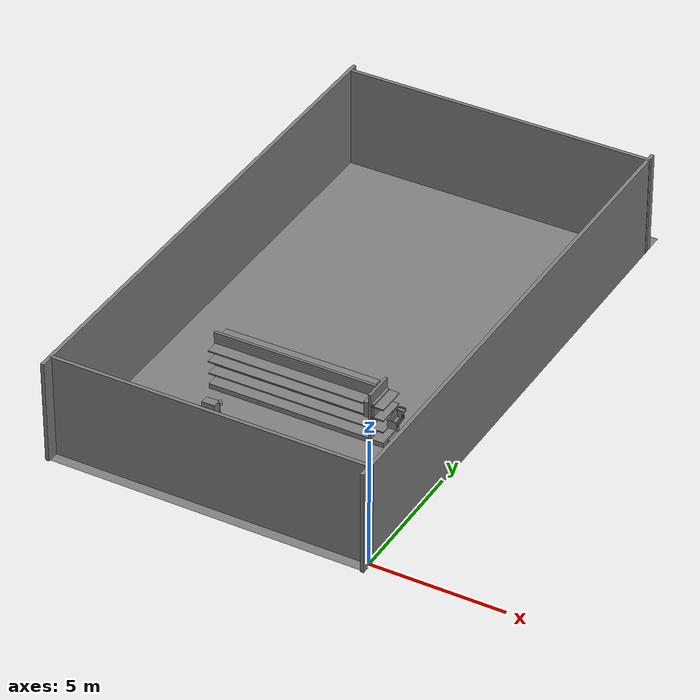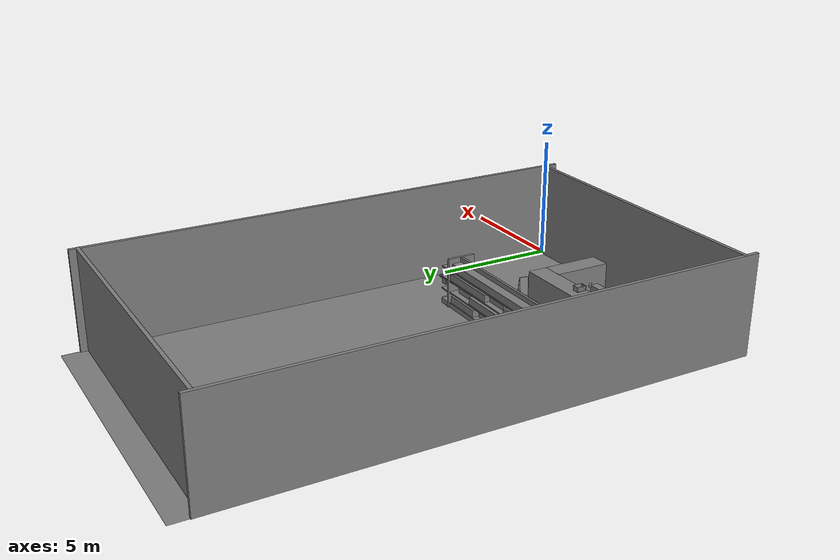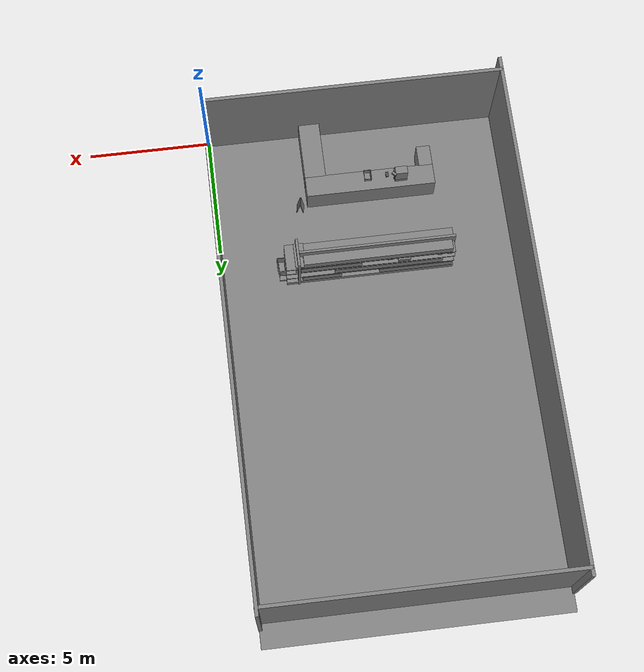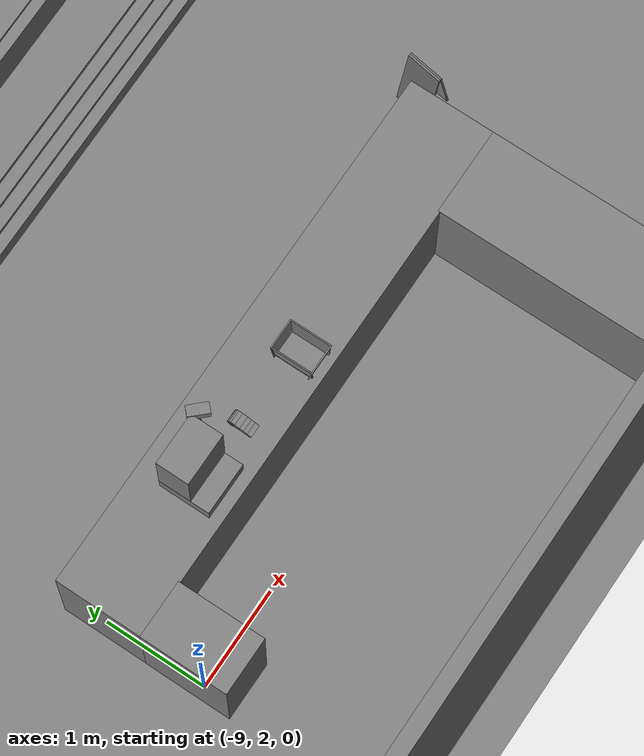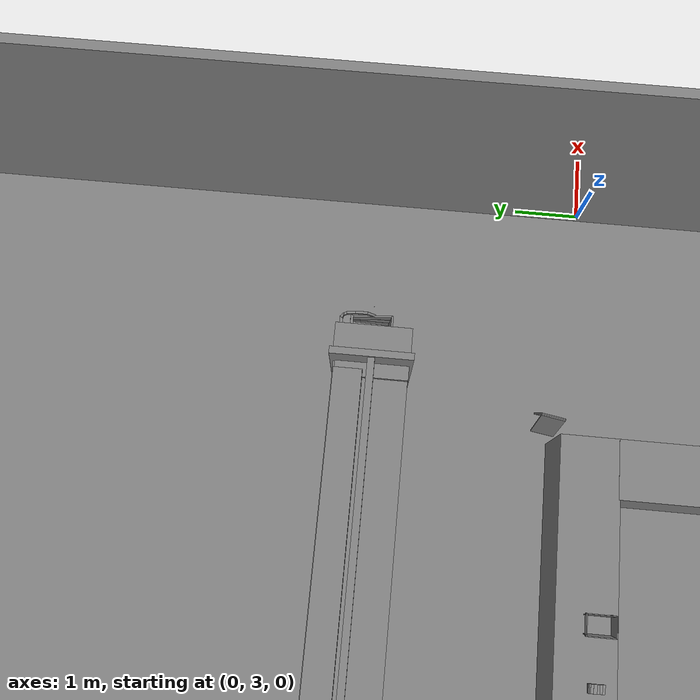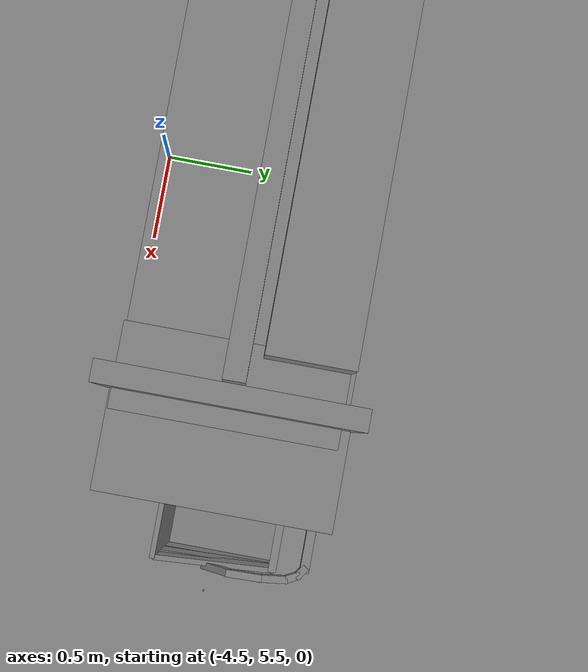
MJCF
<mujoco>
    <option gravity="0.000000000 0.000000000 -9.810000420" timestep="0.0166666" integrator="implicitfast" density="1.225" viscosity="1.8000001e-05" noslip_iterations="10" iterations="100" sdf_iterations="50">
        <flag multiccd="disable"/>
    </option>
    <size memory="1000M"/>
    <compiler coordinate="local"/>
    <worldbody>
        <light cutoff="30" pos="0 1 1" dir="0 -1 -2"/>
        <light cutoff="30" pos="0 -1 1" dir="0 1 -2"/>
        <body pos="-2.436573029 6.404376507 0.137849092" euler="0.000000000 0.000000000 0.000000000" name="openloong_gripper_2f85_fix_base_usda_shoppingtrolley_01">
            <geom contype="1" conaffinity="1" density="1000" type="box" material="" rgba="0.500000000 0.500000000 0.500000000 1.000000000" solimp="0.899999976 0.949999988 0.001000000" friction="1.000000000 0.005000000 0.000100000" solref="0.020000000 1.000000000" margin="0" condim="3" group="0" pos="-0.107458733 0.238907143 0.911498845" quat="0.634576976 0.622505128 -0.330067992 -0.317575932" size="0.017999999 0.022499999 0.035999998" name="openloong_gripper_2f85_fix_base_usda_geom_8FD3EA12_D40E_4CB3_A3E1_083B72E908D3"/>
            <geom contype="1" conaffinity="1" density="1000" type="box" material="" rgba="0.500000000 0.500000000 0.500000000 1.000000000" solimp="0.899999976 0.949999988 0.001000000" friction="1.000000000 0.005000000 0.000100000" solref="0.020000000 1.000000000" margin="0" condim="3" group="0" pos="-0.126757339 -0.182533979 0.598989725" quat="0.996607184 0.055331606 -0.059003651 -0.015205891" size="0.013499999 0.287999988 0.053999998" name="openloong_gripper_2f85_fix_base_usda_geom_72BF7DC2_5079_4315_AC4C_EC1AE8E914A1"/>
            <geom contype="1" conaffinity="1" density="1000" type="box" material="" rgba="0.500000000 0.500000000 0.500000000 1.000000000" solimp="0.899999976 0.949999988 0.001000000" friction="1.000000000 0.005000000 0.000100000" solref="0.020000000 1.000000000" margin="0" condim="3" group="0" pos="-0.005004787 0.248085022 0.912686050" quat="1.000000000 0.000000000 0.000000000 0.000000000" size="0.107999995 0.022499999 0.022499999" name="openloong_gripper_2f85_fix_base_usda_geom_F087012D_A54D_459B_9893_9D8E21154EB2"/>
            <geom contype="1" conaffinity="1" density="1000" type="box" material="" rgba="0.500000000 0.500000000 0.500000000 1.000000000" solimp="0.899999976 0.949999988 0.001000000" friction="1.000000000 0.005000000 0.000100000" solref="0.020000000 1.000000000" margin="0" condim="3" group="0" pos="-0.169898406 -0.043119621 0.915120542" quat="0.687021017 0.726584017 -0.005590606 -0.006832919" size="0.017999999 0.022499999 0.089999996" name="openloong_gripper_2f85_fix_base_usda_geom_1AD353FE_9E79_476F_9A3C_0C8232DD0276"/>
            <geom contype="1" conaffinity="1" density="1000" type="box" material="" rgba="0.500000000 0.500000000 0.500000000 1.000000000" solimp="0.899999976 0.949999988 0.001000000" friction="1.000000000 0.005000000 0.000100000" solref="0.020000000 1.000000000" margin="0" condim="3" group="0" pos="0.148195267 -0.199506566 0.782808602" quat="0.998808920 0.017156634 0.026950166 0.036880098" size="0.013499999 0.305999994 0.063000001" name="openloong_gripper_2f85_fix_base_usda_geom_155B9C5D_CD62_4879_AE28_5E6AEE0AB1DD"/>
            <geom contype="1" conaffinity="1" density="1000" type="box" material="" rgba="0.500000000 0.500000000 0.500000000 1.000000000" solimp="0.899999976 0.949999988 0.001000000" friction="1.000000000 0.005000000 0.000100000" solref="0.020000000 1.000000000" margin="0" condim="3" group="0" pos="-0.142927840 -0.199506134 0.784674108" quat="0.998421252 0.016904408 -0.027109101 -0.046199299" size="0.013499999 0.305999994 0.063000001" name="openloong_gripper_2f85_fix_base_usda_geom_7F5F5265_5802_4990_9A2B_A38F7EFEF91A"/>
            <geom contype="1" conaffinity="1" density="1000" type="box" material="" rgba="0.500000000 0.500000000 0.500000000 1.000000000" solimp="0.899999976 0.949999988 0.001000000" friction="1.000000000 0.005000000 0.000100000" solref="0.020000000 1.000000000" margin="0" condim="3" group="0" pos="-0.000004721 -0.174527690 0.560063601" quat="0.996704638 0.081116498 -0.000000004 0.000000000" size="0.126000002 0.287999988 0.009000000" name="openloong_gripper_2f85_fix_base_usda_geom_5134C14F_C23F_4784_8716_AF9CCB6B8049"/>
            <geom contype="1" conaffinity="1" density="1000" type="box" material="" rgba="0.500000000 0.500000000 0.500000000 1.000000000" solimp="0.899999976 0.949999988 0.001000000" friction="1.000000000 0.005000000 0.000100000" solref="0.020000000 1.000000000" margin="0" condim="3" group="0" pos="-0.160832763 0.103427693 0.910528183" quat="0.711469591 0.699786782 -0.048386075 -0.042050660" size="0.017999999 0.022499999 0.071999997" name="openloong_gripper_2f85_fix_base_usda_geom_FA76133A_A8C3_45C3_B9D2_3CE74A43C8F6"/>
            <geom contype="1" conaffinity="1" density="1000" type="box" material="" rgba="0.500000000 0.500000000 0.500000000 1.000000000" solimp="0.899999976 0.949999988 0.001000000" friction="1.000000000 0.005000000 0.000100000" solref="0.020000000 1.000000000" margin="0" condim="3" group="0" pos="-0.169898406 -0.178061336 0.864131629" quat="0.916343808 -0.400392294 -0.000000045 0.000000030" size="0.017999999 0.022499999 0.089999996" name="openloong_gripper_2f85_fix_base_usda_geom_8DD962CA_7154_4871_9D58_6CA409B7D022"/>
            <geom contype="1" conaffinity="1" density="1000" type="box" material="" rgba="0.500000000 0.500000000 0.500000000 1.000000000" solimp="0.899999976 0.949999988 0.001000000" friction="1.000000000 0.005000000 0.000100000" solref="0.020000000 1.000000000" margin="0" condim="3" group="0" pos="-0.000006008 -0.484932661 0.670727849" quat="0.997585475 0.069449045 -0.000000004 -0.000000089" size="0.179999992 0.013499999 0.170999989" name="openloong_gripper_2f85_fix_base_usda_geom_B9D9F29E_DDE0_4F0B_A057_B6251D65CDEF"/>
            <geom contype="1" conaffinity="1" density="1000" type="box" material="" rgba="0.500000000 0.500000000 0.500000000 1.000000000" solimp="0.899999976 0.949999988 0.001000000" friction="1.000000000 0.005000000 0.000100000" solref="0.020000000 1.000000000" margin="0" condim="3" group="0" pos="0.134013891 0.200098798 0.912192523" quat="0.692574680 -0.680924535 -0.166899428 0.169783980" size="0.017999999 0.022499999 0.035999998" name="openloong_gripper_2f85_fix_base_usda_geom_79B5958E_F5C1_4B83_9441_20156D796DA4"/>
            <geom contype="1" conaffinity="1" density="1000" type="box" material="" rgba="0.500000000 0.500000000 0.500000000 1.000000000" solimp="0.899999976 0.949999988 0.001000000" friction="1.000000000 0.005000000 0.000100000" solref="0.020000000 1.000000000" margin="0" condim="3" group="0" pos="0.141839072 -0.191051379 0.702451229" quat="0.997147262 0.056065105 0.045779929 0.021407485" size="0.013499999 0.287999988 0.053999998" name="openloong_gripper_2f85_fix_base_usda_geom_2A95291C_0A58_4E57_827C_497785B1D5B0"/>
            <geom contype="1" conaffinity="1" density="1000" type="box" material="" rgba="0.500000000 0.500000000 0.500000000 1.000000000" solimp="0.899999976 0.949999988 0.001000000" friction="1.000000000 0.005000000 0.000100000" solref="0.020000000 1.000000000" margin="0" condim="3" group="0" pos="0.169898629 -0.178061336 0.864131629" quat="0.916343808 -0.400392294 -0.000000045 0.000000030" size="0.017999999 0.022499999 0.089999996" name="openloong_gripper_2f85_fix_base_usda_geom_B210FF42_FF84_44C5_A083_22D98E3D2DC1"/>
            <geom contype="1" conaffinity="1" density="1000" type="box" material="" rgba="0.500000000 0.500000000 0.500000000 1.000000000" solimp="0.899999976 0.949999988 0.001000000" friction="1.000000000 0.005000000 0.000100000" solref="0.020000000 1.000000000" margin="0" condim="3" group="0" pos="-0.000005364 0.100332208 0.734785020" quat="0.999668717 0.025737956 -0.000000010 0.000000000" size="0.135000005 0.019800000 0.152999997" name="openloong_gripper_2f85_fix_base_usda_geom_2AB4B3A3_8988_40A4_A5EB_4AAC5BE790AD"/>
            <geom contype="1" conaffinity="1" density="1000" type="box" material="" rgba="0.500000000 0.500000000 0.500000000 1.000000000" solimp="0.899999976 0.949999988 0.001000000" friction="1.000000000 0.005000000 0.000100000" solref="0.020000000 1.000000000" margin="0" condim="3" group="0" pos="-0.012634277 -0.174527690 -0.088243507" quat="1.000000000 0.000000000 -0.000000004 0.000000000" size="0.135000005 0.287999988 0.044999998" name="openloong_gripper_2f85_fix_base_usda_geom_EA4CED05_B237_4E9C_8DA8_B70493866BB5"/>
            <geom contype="1" conaffinity="1" density="1000" type="box" material="" rgba="0.500000000 0.500000000 0.500000000 1.000000000" solimp="0.899999976 0.949999988 0.001000000" friction="1.000000000 0.005000000 0.000100000" solref="0.020000000 1.000000000" margin="0" condim="3" group="0" pos="0.131482959 -0.182533979 0.598989725" quat="0.996607125 0.055331629 0.059003670 0.015205893" size="0.013499999 0.287999988 0.053999998" name="openloong_gripper_2f85_fix_base_usda_geom_56550B19_D9E6_4AD6_91E9_3C0E5F45FB6E"/>
            <geom contype="1" conaffinity="1" density="1000" type="box" material="" rgba="0.500000000 0.500000000 0.500000000 1.000000000" solimp="0.899999976 0.949999988 0.001000000" friction="1.000000000 0.005000000 0.000100000" solref="0.020000000 1.000000000" margin="0" condim="3" group="0" pos="0.103667587 0.233050480 0.912927270" quat="0.634205043 -0.622199059 -0.324503720 0.324576139" size="0.017999999 0.022499999 0.035999998" name="openloong_gripper_2f85_fix_base_usda_geom_DCB38810_4BD3_4C22_BEB9_7A52FEEAD6EB"/>
            <geom contype="1" conaffinity="1" density="1000" type="box" material="" rgba="0.500000000 0.500000000 0.500000000 1.000000000" solimp="0.899999976 0.949999988 0.001000000" friction="1.000000000 0.005000000 0.000100000" solref="0.020000000 1.000000000" margin="0" condim="3" group="0" pos="-0.134013891 0.200098798 0.912192523" quat="0.694057047 0.679413557 -0.172947660 -0.163618833" size="0.017999999 0.022499999 0.035999998" name="openloong_gripper_2f85_fix_base_usda_geom_16081D51_0DD4_497D_9CAF_4DA895D7708E"/>
            <geom contype="1" conaffinity="1" density="1000" type="box" material="" rgba="0.500000000 0.500000000 0.500000000 1.000000000" solimp="0.899999976 0.949999988 0.001000000" friction="1.000000000 0.005000000 0.000100000" solref="0.020000000 1.000000000" margin="0" condim="3" group="0" pos="-0.135714188 -0.191051379 0.694841146" quat="0.997147322 0.056064609 -0.045779683 -0.021407485" size="0.013499999 0.287999988 0.053999998" name="openloong_gripper_2f85_fix_base_usda_geom_5C7D6920_5CD0_489D_8278_4A8D518A8D66"/>
            <geom contype="1" conaffinity="1" density="1000" type="box" material="" rgba="0.500000000 0.500000000 0.500000000 1.000000000" solimp="0.899999976 0.949999988 0.001000000" friction="1.000000000 0.005000000 0.000100000" solref="0.020000000 1.000000000" margin="0" condim="3" group="0" pos="0.169898629 -0.043119621 0.915120542" quat="0.687029123 -0.726576388 -0.006509603 0.005963952" size="0.017999999 0.022499999 0.089999996" name="openloong_gripper_2f85_fix_base_usda_geom_BE10ED20_0725_4C9A_AE3D_67FDD409840F"/>
            <geom contype="1" conaffinity="1" density="1000" type="box" material="" rgba="0.500000000 0.500000000 0.500000000 1.000000000" solimp="0.899999976 0.949999988 0.001000000" friction="1.000000000 0.005000000 0.000100000" solref="0.020000000 1.000000000" margin="0" condim="3" group="0" pos="0.160832971 0.103427693 0.910528183" quat="0.711112797 -0.700149298 -0.042821646 0.047705106" size="0.017999999 0.022499999 0.071999997" name="openloong_gripper_2f85_fix_base_usda_geom_A44F4126_2A0C_4265_9148_1BB4A667DE82"/>
            <freejoint name="openloong_gripper_2f85_fix_base_usda_shoppingtrolley_01_joint"/>
            <site size="0.005000000 0.005000000 0.005000000" rgba="0.500000000 0.500000000 0.500000000 1.000000000" pos="0.000000000 0.000000000 0.000000000" quat="1.000000000 0.000000000 0.000000000 0.000000000" group="0" type="sphere" name="openloong_gripper_2f85_fix_base_usda_shoppingtrolley_01"/>
        </body>
        <body pos="-7.168000221 2.823999882 1.227496982" euler="-0.283413887 0.056829713 -0.133293241" name="openloong_gripper_2f85_fix_base_usda_Pos">
            <geom contype="1" conaffinity="1" density="1000" type="box" material="" rgba="0.500000000 0.500000000 0.500000000 1.000000000" solimp="0.899999976 0.949999988 0.001000000" friction="1.000000000 0.005000000 0.000100000" solref="0.020000000 1.000000000" margin="0" condim="3" group="0" pos="-0.002278805 0.074524641 -0.004134178" quat="0.315989256 0.948762834 0.000000000 0.000000000" size="0.059999999 0.013000000 0.035000000" name="openloong_gripper_2f85_fix_base_usda_geom_D40AD19C_3CF0_41AC_9E16_4B3CF7148750"/>
            <geom contype="1" conaffinity="1" density="1000" type="box" material="" rgba="0.500000000 0.500000000 0.500000000 1.000000000" solimp="0.899999976 0.949999988 0.001000000" friction="1.000000000 0.005000000 0.000100000" solref="0.020000000 1.000000000" margin="0" condim="3" group="0" pos="-0.002278805 0.078031301 0.008128285" quat="0.990447283 -0.137893349 -0.000000000 0.000000000" size="0.059999999 0.010000000 0.035000000" name="openloong_gripper_2f85_fix_base_usda_geom_8B235685_C488_48D1_8274_0821689B3541"/>
            <geom contype="1" conaffinity="1" density="1000" type="box" material="" rgba="0.500000000 0.500000000 0.500000000 1.000000000" solimp="0.899999976 0.949999988 0.001000000" friction="1.000000000 0.005000000 0.000100000" solref="0.020000000 1.000000000" margin="0" condim="3" group="0" pos="-0.002278805 0.080785275 -0.002596974" quat="0.287325412 -0.957833171 0.000000000 -0.000000000" size="0.059999999 0.013000000 0.035000000" name="openloong_gripper_2f85_fix_base_usda_geom_E9FBFCDC_6436_4ADB_A80C_43B996CBF358"/>
            <geom contype="1" conaffinity="1" density="1000" type="box" material="" rgba="0.500000000 0.500000000 0.500000000 1.000000000" solimp="0.899999976 0.949999988 0.001000000" friction="1.000000000 0.005000000 0.000100000" solref="0.020000000 1.000000000" margin="0" condim="3" group="0" pos="-0.002278805 -0.098804474 -0.020147085" quat="0.988851428 0.148906425 0.000000000 -0.000000000" size="0.059999999 0.022000000 0.020000000" name="openloong_gripper_2f85_fix_base_usda_geom_D1B9BBB9_24D2_40B9_A246_DC2F781F7481"/>
            <geom contype="1" conaffinity="1" density="1000" type="box" material="" rgba="0.500000000 0.500000000 0.500000000 1.000000000" solimp="0.899999976 0.949999988 0.001000000" friction="1.000000000 0.005000000 0.000100000" solref="0.020000000 1.000000000" margin="0" condim="3" group="0" pos="-0.002279282 0.019920349 0.012102842" quat="0.995421529 0.095583312 -0.000000000 0.000000000" size="0.059999999 0.025000000 0.026000001" name="openloong_gripper_2f85_fix_base_usda_geom_0752B644_56BF_4B12_9926_F69D0FF1F2E4"/>
            <geom contype="1" conaffinity="1" density="1000" type="box" material="" rgba="0.500000000 0.500000000 0.500000000 1.000000000" solimp="0.899999976 0.949999988 0.001000000" friction="1.000000000 0.005000000 0.000100000" solref="0.020000000 1.000000000" margin="0" condim="3" group="0" pos="-0.002279282 0.005734444 -0.014276981" quat="0.999571502 -0.029275293 -0.000000000 0.000000000" size="0.059999999 0.050000001 0.010000000" name="openloong_gripper_2f85_fix_base_usda_geom_C8FED0CF_A3A9_4388_BCA0_69564309D7A1"/>
            <geom contype="1" conaffinity="1" density="1000" type="box" material="" rgba="0.500000000 0.500000000 0.500000000 1.000000000" solimp="0.899999976 0.949999988 0.001000000" friction="1.000000000 0.005000000 0.000100000" solref="0.020000000 1.000000000" margin="0" condim="3" group="0" pos="-0.002278805 0.079460382 0.007771969" quat="0.922590315 -0.385781497 -0.000000000 0.000000000" size="0.059999999 0.010000000 0.035000000" name="openloong_gripper_2f85_fix_base_usda_geom_80D1EBA9_3005_4FBE_80F1_FFEFF9F11644"/>
            <geom contype="1" conaffinity="1" density="1000" type="box" material="" rgba="0.500000000 0.500000000 0.500000000 1.000000000" solimp="0.899999976 0.949999988 0.001000000" friction="1.000000000 0.005000000 0.000100000" solref="0.020000000 1.000000000" margin="0" condim="3" group="0" pos="-0.002279282 0.081384182 -0.001320124" quat="0.590483606 -0.807049692 0.000000000 0.000000000" size="0.059999999 0.013000000 0.035000000" name="openloong_gripper_2f85_fix_base_usda_geom_15C25751_128B_46FF_95D5_0C411A2B450E"/>
            <geom contype="1" conaffinity="1" density="1000" type="box" material="" rgba="0.500000000 0.500000000 0.500000000 1.000000000" solimp="0.899999976 0.949999988 0.001000000" friction="1.000000000 0.005000000 0.000100000" solref="0.020000000 1.000000000" margin="0" condim="3" group="0" pos="-0.002278805 -0.059297562 -0.007972836" quat="0.988851428 0.148906425 0.000000000 -0.000000000" size="0.059999999 0.020000000 0.022000000" name="openloong_gripper_2f85_fix_base_usda_geom_22912631_30B3_4834_9D0C_7C07D3389D86"/>
            <geom contype="1" conaffinity="1" density="1000" type="box" material="" rgba="0.500000000 0.500000000 0.500000000 1.000000000" solimp="0.899999976 0.949999988 0.001000000" friction="1.000000000 0.005000000 0.000100000" solref="0.020000000 1.000000000" margin="0" condim="3" group="0" pos="-0.002278805 0.076618671 -0.004656911" quat="0.004634960 0.999989390 -0.000000000 0.000000000" size="0.059999999 0.013000000 0.035000000" name="openloong_gripper_2f85_fix_base_usda_geom_B39CA72D_9991_4D9E_9DA4_A92B10D778C8"/>
            <geom contype="1" conaffinity="1" density="1000" type="box" material="" rgba="0.500000000 0.500000000 0.500000000 1.000000000" solimp="0.899999976 0.949999988 0.001000000" friction="1.000000000 0.005000000 0.000100000" solref="0.020000000 1.000000000" margin="0" condim="3" group="0" pos="-0.002279282 -0.021952629 0.002959967" quat="0.991270185 0.131847635 0.000000000 -0.000000000" size="0.059999999 0.020000000 0.024000000" name="openloong_gripper_2f85_fix_base_usda_geom_47B232BC_157E_4C6A_9A4B_B91BD203CFE8"/>
            <geom contype="1" conaffinity="1" density="1000" type="box" material="" rgba="0.500000000 0.500000000 0.500000000 1.000000000" solimp="0.899999976 0.949999988 0.001000000" friction="1.000000000 0.005000000 0.000100000" solref="0.020000000 1.000000000" margin="0" condim="3" group="0" pos="-0.002278805 0.081418991 0.002587795" quat="0.803492188 -0.595315576 0.000000000 0.000000000" size="0.059999999 0.013000000 0.035000000" name="openloong_gripper_2f85_fix_base_usda_geom_F528F351_29F5_43CA_81F5_71AC3F168AE3"/>
            <geom contype="1" conaffinity="1" density="1000" type="box" material="" rgba="0.500000000 0.500000000 0.500000000 1.000000000" solimp="0.899999976 0.949999988 0.001000000" friction="1.000000000 0.005000000 0.000100000" solref="0.020000000 1.000000000" margin="0" condim="3" group="0" pos="-0.002278805 0.061115503 0.008545756" quat="0.999325931 0.036714435 -0.000000000 -0.000000000" size="0.059999999 0.020000000 0.035000000" name="openloong_gripper_2f85_fix_base_usda_geom_8A5FB7B5_AE06_43F8_9F51_7CE26319E0D0"/>
            <freejoint name="openloong_gripper_2f85_fix_base_usda_pos_scan"/>
        </body>
        <body pos="-3.510578632 3.403555870 -0.000000100" euler="0.000000000 0.000000000 40.200675964" name="openloong_gripper_2f85_fix_base_usda_PZ">
            <geom contype="1" conaffinity="1" density="1000" type="box" material="" rgba="0.500000000 0.500000000 0.500000000 1.000000000" solimp="0.899999976 0.949999988 0.001000000" friction="1.000000000 0.005000000 0.000100000" solref="0.020000000 1.000000000" margin="0" condim="3" group="0" pos="-0.047453165 0.056484699 0.373715430" quat="0.934750080 0.077914521 0.028795123 0.345459938" size="0.180000007 0.010000000 0.379999995" name="openloong_gripper_2f85_fix_base_usda_geom_2D632CF3_C015_4A4C_AB48_D9495E70CCFD"/>
            <geom contype="1" conaffinity="1" density="1000" type="box" material="" rgba="0.500000000 0.500000000 0.500000000 1.000000000" solimp="0.899999976 0.949999988 0.001000000" friction="1.000000000 0.005000000 0.000100000" solref="0.020000000 1.000000000" margin="0" condim="3" group="0" pos="0.047452450 -0.054376602 0.374072611" quat="0.934387863 -0.082143910 -0.030358355 0.345326364" size="0.180000007 0.010000000 0.379999995" name="openloong_gripper_2f85_fix_base_usda_geom_0FA8364A_6A0E_44B3_B077_10CF89897F5E"/>
            <freejoint name="openloong_gripper_2f85_fix_base_usda_PZ"/>
        </body>
        <body pos="-6.332345009 2.779978037 1.034067392" euler="0.000000000 0.000000000 0.000000000" name="openloong_gripper_2f85_fix_base_usda_basket">
            <geom contype="1" conaffinity="1" density="100000" type="box" material="" rgba="0.500000000 0.500000000 0.500000000 1.000000000" solimp="0.899999976 0.949999988 0.001000000" friction="1.000000000 0.899999976 0.000100000" solref="0.020000000 1.000000000" margin="0" condim="3" group="0" pos="-0.039724827 -0.188568115 0.167089701" quat="0.997537494 0.070135131 0.000000000 0.000000000" size="0.150000006 0.006000000 0.108000003" name="openloong_gripper_2f85_fix_base_usda_geom_F03F411D_2A88_4875_816A_9034A315221C"/>
            <geom contype="1" conaffinity="1" density="100000" type="box" material="" rgba="0.500000000 0.500000000 0.500000000 1.000000000" solimp="0.899999976 0.949999988 0.001000000" friction="1.000000000 0.899999976 0.000100000" solref="0.020000000 1.000000000" margin="0" condim="3" group="0" pos="0.094372749 0.000000000 0.168361664" quat="0.706172049 0.036353335 0.036353379 0.706171215" size="0.200000003 0.006000000 0.108000003" name="openloong_gripper_2f85_fix_base_usda_geom_358DE682_9753_450B_B48F_31AA46E5EC59"/>
            <geom contype="1" conaffinity="1" density="100000" type="box" material="" rgba="0.500000000 0.500000000 0.500000000 1.000000000" solimp="0.899999976 0.949999988 0.001000000" friction="1.000000000 0.899999976 0.000100000" solref="0.020000000 1.000000000" margin="0" condim="3" group="0" pos="-0.039724827 0.000000000 0.068126202" quat="1.000000000 0.000000000 0.000000000 0.000000000" size="0.129999995 0.174999997 0.006000000" name="openloong_gripper_2f85_fix_base_usda_geom_93B2F905_F5EB_4658_8948_18AB790CD1E9"/>
            <geom contype="1" conaffinity="1" density="100000" type="box" material="" rgba="0.500000000 0.500000000 0.500000000 1.000000000" solimp="0.899999976 0.949999988 0.001000000" friction="1.000000000 0.899999976 0.000100000" solref="0.020000000 1.000000000" margin="0" condim="3" group="0" pos="-0.039724827 0.188377380 0.167089701" quat="0.997489929 -0.070808925 0.000000000 0.000000000" size="0.150000006 0.006000000 0.108000003" name="openloong_gripper_2f85_fix_base_usda_geom_C0FE3E7E_0D10_4564_894B_56C75F8C4B0D"/>
            <geom contype="1" conaffinity="1" density="100000" type="box" material="" rgba="0.500000000 0.500000000 0.500000000 1.000000000" solimp="0.899999976 0.949999988 0.001000000" friction="1.000000000 0.899999976 0.000100000" solref="0.020000000 1.000000000" margin="0" condim="3" group="0" pos="-0.172339439 0.000000000 0.168361664" quat="0.706172407 -0.036353018 -0.036353093 0.706170976" size="0.200000003 0.006000000 0.108000003" name="openloong_gripper_2f85_fix_base_usda_geom_B34E9357_400D_437D_8A88_E25B63E4C93C"/>
            <freejoint name="openloong_gripper_2f85_fix_base_usda_basket_joint"/>
            <site size="0.005000000 0.005000000 0.005000000" rgba="0.500000000 0.500000000 0.500000000 1.000000000" pos="0.000000000 0.000000000 0.000000000" quat="1.000000000 0.000000000 0.000000000 0.000000000" group="0" type="sphere" name="openloong_gripper_2f85_fix_base_usda_basketsite"/>
        </body>
        <body pos="0.000000000 0.000000000 0.000000000" euler="0.000000000 0.000000000 0.000000000" name=" Static Objects_ Static Objects">
            <geom contype="1" conaffinity="1" density="1000" type="box" material="" rgba="0.500000000 0.500000000 0.500000000 1.000000000" solimp="0.899999976 0.949999988 0.001000000" friction="1.000000000 0.005000000 0.000100000" solref="0.020000000 1.000000000" margin="0" condim="3" group="0" pos="-6.286010742 6.153595448 1.563861728" quat="0.707107067 0.000000000 0.000000000 0.707106471" size="0.529999971 3.134999990 0.025000000" name=" Static Objects_geom_3F787501_C60C_4F80_986D_7D8D549DDF22"/>
            <geom contype="1" conaffinity="1" density="1000" type="box" material="" rgba="0.500000000 0.500000000 0.500000000 1.000000000" solimp="0.899999976 0.949999988 0.001000000" friction="1.000000000 0.005000000 0.000100000" solref="0.020000000 1.000000000" margin="0" condim="3" group="0" pos="-3.101639986 6.150595188 1.018643856" quat="1.000000000 0.000000000 0.000000000 0.000000000" size="0.050000001 0.579999983 1.019999981" name=" Static Objects_geom_59D355B0_7FF3_44D2_B9F4_4A67D6554835"/>
            <geom contype="1" conaffinity="1" density="1000" type="box" material="" rgba="0.500000000 0.500000000 0.500000000 1.000000000" solimp="0.899999976 0.949999988 0.001000000" friction="1.000000000 0.005000000 0.000100000" solref="0.020000000 1.000000000" margin="0" condim="3" group="0" pos="-2.825197220 6.153595448 1.563861728" quat="0.707107067 0.000000000 0.000000000 0.707106471" size="0.550000012 0.239999995 0.025000000" name=" Static Objects_geom_A95A703F_D2C2_4DE6_BC9D_A8CFEE6E8B39"/>
            <geom contype="1" conaffinity="1" density="1000" type="box" material="" rgba="0.500000000 0.500000000 0.500000000 1.000000000" solimp="0.899999976 0.949999988 0.001000000" friction="1.000000000 0.005000000 0.000100000" solref="0.020000000 1.000000000" margin="0" condim="3" group="0" pos="-6.311686516 6.153595448 1.018643856" quat="0.707107067 0.000000000 0.000000000 0.707106471" size="0.050000001 3.150000095 1.019999981" name=" Static Objects_geom_5D13CACD_151B_4BC1_B05F_358287C56AA0"/>
            <geom contype="1" conaffinity="1" density="1000" type="box" material="" rgba="0.500000000 0.500000000 0.500000000 1.000000000" solimp="0.899999976 0.949999988 0.001000000" friction="1.000000000 0.005000000 0.000100000" solref="0.020000000 1.000000000" margin="0" condim="3" group="0" pos="-2.825197220 6.153595448 1.115278244" quat="0.707107067 0.000000000 0.000000000 0.707106471" size="0.550000012 0.239999995 0.025000000" name=" Static Objects_geom_87C65AA6_B981_4985_9FFE_D8945D80C467"/>
            <geom contype="1" conaffinity="1" density="1000" type="box" material="" rgba="0.500000000 0.500000000 0.500000000 1.000000000" solimp="0.899999976 0.949999988 0.001000000" friction="1.000000000 0.005000000 0.000100000" solref="0.020000000 1.000000000" margin="0" condim="3" group="0" pos="-6.293097973 6.153595448 1.114443064" quat="0.707107067 0.000000000 0.000000000 0.707106471" size="0.529999971 3.134999990 0.025000000" name=" Static Objects_geom_71FD2B0F_2E51_414A_824C_7B8FAA71F26D"/>
            <geom contype="1" conaffinity="1" density="1000" type="box" material="" rgba="0.500000000 0.500000000 0.500000000 1.000000000" solimp="0.899999976 0.949999988 0.001000000" friction="1.000000000 0.005000000 0.000100000" solref="0.020000000 1.000000000" margin="0" condim="3" group="0" pos="-2.825197220 6.153595448 0.629031777" quat="0.707107067 0.000000000 0.000000000 0.707106471" size="0.550000012 0.239999995 0.025000000" name=" Static Objects_geom_13EB09A6_D3A7_4483_915E_D4E1F924B342"/>
            <geom contype="1" conaffinity="1" density="1000" type="box" material="" rgba="0.500000000 0.500000000 0.500000000 1.000000000" solimp="0.899999976 0.949999988 0.001000000" friction="1.000000000 0.005000000 0.000100000" solref="0.020000000 1.000000000" margin="0" condim="3" group="0" pos="-6.286010742 6.153595448 0.096129179" quat="0.707107067 0.000000000 0.000000000 0.707106471" size="0.529999971 3.134999990 0.098999999" name=" Static Objects_geom_DD5E2266_3E35_42A2_BA03_6171ADEC349B"/>
            <geom contype="1" conaffinity="1" density="1000" type="box" material="" rgba="0.500000000 0.500000000 0.500000000 1.000000000" solimp="0.899999976 0.949999988 0.001000000" friction="1.000000000 0.005000000 0.000100000" solref="0.020000000 1.000000000" margin="0" condim="3" group="0" pos="-2.825197220 6.153595448 0.097434282" quat="0.707107067 0.000000000 0.000000000 0.707106471" size="0.550000012 0.239999995 0.098999999" name=" Static Objects_geom_A2EDFA0A_D69D_4C12_9F75_5FCC1E986855"/>
            <geom contype="1" conaffinity="1" density="1000" type="box" material="" rgba="0.500000000 0.500000000 0.500000000 1.000000000" solimp="0.899999976 0.949999988 0.001000000" friction="1.000000000 0.005000000 0.000100000" solref="0.020000000 1.000000000" margin="0" condim="3" group="0" pos="-6.286010742 6.153595448 0.629031777" quat="0.707107067 0.000000000 0.000000000 0.707106471" size="0.529999971 3.134999990 0.025000000" name=" Static Objects_geom_8B5D7B23_06DA_4FFC_B021_195BEC6F555D"/>
            <geom contype="1" conaffinity="1" density="1000" type="box" material="" rgba="0.500000000 0.500000000 0.500000000 1.000000000" solimp="0.899999976 0.949999988 0.001000000" friction="1.000000000 0.005000000 0.000100000" solref="0.020000000 1.000000000" margin="0" condim="3" group="0" pos="-6.000000000 20.159999847 2.000000000" quat="1.000000000 0.000000000 0.000000000 0.000000000" size="6.079999924 0.070000000 2.000000000" name=" Static Objects_geom_4EB5C402_D9E9_4AC5_BEC6_9700C7F7AA9A"/>
            <geom contype="1" conaffinity="1" density="1000" type="box" material="" rgba="0.500000000 0.500000000 0.500000000 1.000000000" solimp="0.899999976 0.949999988 0.001000000" friction="1.000000000 0.005000000 0.000100000" solref="0.020000000 1.000000000" margin="0" condim="3" group="0" pos="-6.000000000 0.035000000 2.000000000" quat="1.000000000 0.000000000 0.000000000 0.000000000" size="6.079999924 0.070000000 2.000000000" name=" Static Objects_geom_7F391B1D_03DB_4186_9D72_2ADC0EC74D5E"/>
            <geom contype="1" conaffinity="1" density="1000" type="box" material="" rgba="0.500000000 0.500000000 0.500000000 1.000000000" solimp="0.899999976 0.949999988 0.001000000" friction="1.000000000 0.005000000 0.000100000" solref="0.020000000 1.000000000" margin="0" condim="3" group="0" pos="0.000000000 10.000000000 2.000000000" quat="1.000000000 0.000000000 0.000000000 0.000000000" size="0.070000000 10.500000000 2.000000000" name=" Static Objects_geom_0204EBF6_D3AA_44C9_95C5_C138B9FC2AD1"/>
            <geom contype="1" conaffinity="1" density="1000" type="box" material="" rgba="0.500000000 0.500000000 0.500000000 1.000000000" solimp="0.899999976 0.949999988 0.001000000" friction="1.000000000 0.005000000 0.000100000" solref="0.020000000 1.000000000" margin="0" condim="3" group="0" pos="-12.050000191 10.000000000 2.000000000" quat="1.000000000 0.000000000 0.000000000 0.000000000" size="0.070000000 10.500000000 2.000000000" name=" Static Objects_geom_C2C54AC6_FCEA_4CD2_A0A8_F20117CF3EE4"/>
            <geom contype="1" conaffinity="1" density="1000" type="plane" material="" rgba="0.500000000 0.500000000 0.500000000 1.000000000" solimp="0.899999976 0.949999988 0.001000000" friction="1.000000000 0.005000000 0.000100000" solref="0.020000000 1.000000000" margin="0" condim="3" group="0" pos="-6.000000000 10.399999619 0.000000000" quat="1.000000000 0.000000000 0.000000000 0.000000000" size="6.050000191 10.800000191 0.010000000" name=" Static Objects_geom_264D21FB_3522_4CB4_AE0A_2E3809B6ABB9"/>
            <geom contype="1" conaffinity="1" density="1000" type="box" material="" rgba="0.500000000 0.500000000 0.500000000 1.000000000" solimp="0.899999976 0.949999988 0.001000000" friction="1.000000000 0.005000000 0.000100000" solref="0.020000000 1.000000000" margin="0" condim="3" group="0" pos="-8.830721855 2.096410990 0.549305558" quat="1.000000000 0.000000000 0.000000000 0.000000000" size="0.280000001 0.430000007 0.550000012" name=" Static Objects_geom_39434665_1C3D_4321_A443_BA5C01303590"/>
            <geom contype="1" conaffinity="1" density="1000" type="box" material="" rgba="0.500000000 0.500000000 0.500000000 1.000000000" solimp="0.899999976 0.949999988 0.001000000" friction="1.000000000 0.005000000 0.000100000" solref="0.020000000 1.000000000" margin="0" condim="3" group="0" pos="-6.460197449 2.937205315 0.548931718" quat="1.000000000 0.000000000 0.000000000 0.000000000" size="2.650000095 0.430000007 0.550000012" name=" Static Objects_geom_D164E542_A33E_470F_8501_BD4CB88B8E7B"/>
            <geom contype="1" conaffinity="1" density="1000" type="box" material="" rgba="0.500000000 0.500000000 0.500000000 1.000000000" solimp="0.899999976 0.949999988 0.001000000" friction="1.000000000 0.005000000 0.000100000" solref="0.020000000 1.000000000" margin="0" condim="3" group="0" pos="-4.240264893 1.327049494 0.549888909" quat="1.000000000 0.000000000 0.000000000 0.000000000" size="0.430000007 1.200000048 0.550000012" name=" Static Objects_geom_68250CF5_6296_4DF9_9F17_7B28D1233E32"/>
            <geom contype="1" conaffinity="1" density="1000" type="box" material="" rgba="0.500000000 0.500000000 0.500000000 1.000000000" solimp="0.899999976 0.949999988 0.001000000" friction="1.000000000 0.005000000 0.000100000" solref="0.020000000 1.000000000" margin="0" condim="3" group="0" pos="-7.408766270 3.088089943 1.776644945" quat="0.928051054 0.000000000 0.000000000 0.372453064" size="0.050000001 0.100000001 0.050000001" name=" Static Objects_geom_1D82E84C_CE21_4558_9948_1711C0E709DA"/>
            <geom contype="1" conaffinity="1" density="1000" type="box" material="" rgba="0.500000000 0.500000000 0.500000000 1.000000000" solimp="0.899999976 0.949999988 0.001000000" friction="1.000000000 0.005000000 0.000100000" solref="0.020000000 1.000000000" margin="0" condim="3" group="0" pos="-7.437745571 3.067511320 1.289965630" quat="1.000000000 0.000000000 0.000000000 0.000000000" size="0.029999999 0.020000000 0.020000000" name=" Static Objects_geom_670B85EC_CF74_4ABD_A264_92FF88AA7EDA"/>
            <geom contype="1" conaffinity="1" density="1000" type="box" material="" rgba="0.500000000 0.500000000 0.500000000 1.000000000" solimp="0.899999976 0.949999988 0.001000000" friction="1.000000000 0.005000000 0.000100000" solref="0.020000000 1.000000000" margin="0" condim="3" group="0" pos="-7.719123363 2.867671013 1.173410416" quat="1.000000000 0.000000000 0.000000000 0.000000000" size="0.250000000 0.250000000 0.079999998" name=" Static Objects_geom_A5B2B39D_DCC1_4BEE_919F_DC2BA4241EAD"/>
            <geom contype="1" conaffinity="1" density="1000" type="box" material="" rgba="0.500000000 0.500000000 0.500000000 1.000000000" solimp="0.899999976 0.949999988 0.001000000" friction="1.000000000 0.005000000 0.000100000" solref="0.020000000 1.000000000" margin="0" condim="3" group="0" pos="-7.719123363 2.958004713 1.530241251" quat="1.000000000 0.000000000 0.000000000 0.000000000" size="0.250000000 0.159999996 0.280000001" name=" Static Objects_geom_C4A8F6E6_22FC_4893_815D_D7712D18BE13"/>
            <geom contype="1" conaffinity="1" density="1000" type="cylinder" material="" rgba="0.500000000 0.500000000 0.500000000 1.000000000" solimp="0.899999976 0.949999988 0.001000000" friction="1.000000000 0.005000000 0.000100000" solref="0.020000000 1.000000000" margin="0" condim="3" group="0" pos="-7.427312374 3.069516420 1.502544641" quat="0.928051054 0.000000000 0.000000000 0.372453064" size="0.015000000 0.230000004 0.100000001" name=" Static Objects_geom_218B4AD1_5609_47D7_BF67_3E8D7F697E3B"/>
            <geom contype="1" conaffinity="1" density="1000" type="box" material="" rgba="0.500000000 0.500000000 0.500000000 1.000000000" solimp="0.899999976 0.949999988 0.001000000" friction="1.000000000 0.005000000 0.000100000" solref="0.020000000 1.000000000" margin="0" condim="3" group="0" pos="-9.058088303 6.434794426 1.209077358" quat="1.000000000 0.000000000 0.000000000 0.000000000" size="0.250000000 0.100000001 0.070000000" name=" Static Objects_geom_A4C5BDDA_793B_4EC4_97B8_D2C6A0389EF8"/>
            <geom contype="1" conaffinity="1" density="1000" type="box" material="" rgba="0.500000000 0.500000000 0.500000000 1.000000000" solimp="0.899999976 0.949999988 0.001000000" friction="1.000000000 0.005000000 0.000100000" solref="0.020000000 1.000000000" margin="0" condim="3" group="0" pos="-5.611940861 6.318420410 0.350975692" quat="1.000000000 0.000000000 0.000000000 0.000000000" size="0.699999988 0.100000001 0.150000006" name=" Static Objects_geom_9AF2E2AD_17D0_4B2A_B7FC_41D2055CA0E7"/>
            <geom contype="1" conaffinity="1" density="1000" type="box" material="" rgba="0.500000000 0.500000000 0.500000000 1.000000000" solimp="0.899999976 0.949999988 0.001000000" friction="1.000000000 0.005000000 0.000100000" solref="0.020000000 1.000000000" margin="0" condim="3" group="0" pos="-9.237723351 6.464855671 1.209077358" quat="1.000000000 0.000000000 0.000000000 0.000000000" size="0.100000001 0.100000001 0.070000000" name=" Static Objects_geom_0436A0FA_85D5_4B48_B144_C1167D3D7906"/>
            <geom contype="1" conaffinity="1" density="1000" type="box" material="" rgba="0.500000000 0.500000000 0.500000000 1.000000000" solimp="0.899999976 0.949999988 0.001000000" friction="1.000000000 0.005000000 0.000100000" solref="0.020000000 1.000000000" margin="0" condim="3" group="0" pos="-6.300771236 6.459744930 1.744376063" quat="1.000000000 0.000000000 0.000000000 0.000000000" size="3.000000000 0.200000003 0.150000006" name=" Static Objects_geom_C64C7A30_48A2_4F69_8D44_68EF196E945B"/>
            <geom contype="1" conaffinity="1" density="1000" type="box" material="" rgba="0.500000000 0.500000000 0.500000000 1.000000000" solimp="0.899999976 0.949999988 0.001000000" friction="1.000000000 0.005000000 0.000100000" solref="0.020000000 1.000000000" margin="0" condim="3" group="0" pos="-7.373087406 6.458900928 1.214329123" quat="1.000000000 0.000000000 0.000000000 0.000000000" size="0.250000000 0.200000003 0.075000003" name=" Static Objects_geom_8AF77C82_DFA5_4998_BE36_7C25C04652BF"/>
            <geom contype="1" conaffinity="1" density="1000" type="box" material="" rgba="0.500000000 0.500000000 0.500000000 1.000000000" solimp="0.899999976 0.949999988 0.001000000" friction="1.000000000 0.005000000 0.000100000" solref="0.020000000 1.000000000" margin="0" condim="3" group="0" pos="-4.035642624 6.459744930 0.352518857" quat="1.000000000 0.000000000 0.000000000 0.000000000" size="0.800000012 0.200000003 0.150000006" name=" Static Objects_geom_43E143B7_DF17_451C_AF7F_CD4D5D2B3DE8"/>
            <geom contype="1" conaffinity="1" density="1000" type="box" material="" rgba="0.500000000 0.500000000 0.500000000 1.000000000" solimp="0.899999976 0.949999988 0.001000000" friction="1.000000000 0.005000000 0.000100000" solref="0.020000000 1.000000000" margin="0" condim="3" group="0" pos="-3.907610416 6.318625927 0.800981164" quat="1.000000000 0.000000000 0.000000000 0.000000000" size="0.500000000 0.100000001 0.150000006" name=" Static Objects_geom_B4B0660E_0D3D_4127_A590_1F523DD95DFB"/>
            <geom contype="1" conaffinity="1" density="1000" type="box" material="" rgba="0.500000000 0.500000000 0.500000000 1.000000000" solimp="0.899999976 0.949999988 0.001000000" friction="1.000000000 0.005000000 0.000100000" solref="0.020000000 1.000000000" margin="0" condim="3" group="0" pos="-6.098561764 6.327973843 1.292199373" quat="1.000000000 0.000000000 0.000000000 0.000000000" size="0.500000000 0.100000001 0.150000006" name=" Static Objects_geom_4520C00E_C8B6_4F76_B1D4_56244FB5A386"/>
            <geom contype="1" conaffinity="1" density="1000" type="box" material="" rgba="0.500000000 0.500000000 0.500000000 1.000000000" solimp="0.899999976 0.949999988 0.001000000" friction="1.000000000 0.005000000 0.000100000" solref="0.020000000 1.000000000" margin="0" condim="3" group="0" pos="-7.886891365 6.459744930 0.352518857" quat="1.000000000 0.000000000 0.000000000 0.000000000" size="1.500000000 0.200000003 0.150000006" name=" Static Objects_geom_73637698_92A7_4DFA_8C7E_60A0C5DCA560"/>
            <geom contype="1" conaffinity="1" density="1000" type="box" material="" rgba="0.500000000 0.500000000 0.500000000 1.000000000" solimp="0.899999976 0.949999988 0.001000000" friction="1.000000000 0.005000000 0.000100000" solref="0.020000000 1.000000000" margin="0" condim="3" group="0" pos="-6.824534416 6.447464466 1.212718010" quat="1.000000000 0.000000000 0.000000000 0.000000000" size="0.100000001 0.100000001 0.075000003" name=" Static Objects_geom_5A51042C_F290_4CEE_90A0_C34134FCD191"/>
            <geom contype="1" conaffinity="1" density="1000" type="box" material="" rgba="0.500000000 0.500000000 0.500000000 1.000000000" solimp="0.899999976 0.949999988 0.001000000" friction="1.000000000 0.005000000 0.000100000" solref="0.020000000 1.000000000" margin="0" condim="3" group="0" pos="-4.407354832 6.459744930 1.292199373" quat="1.000000000 0.000000000 0.000000000 0.000000000" size="1.240000010 0.200000003 0.150000006" name=" Static Objects_geom_DB883075_F2A0_4DE3_855D_A254996CA057"/>
            <geom contype="1" conaffinity="1" density="1000" type="box" material="" rgba="0.500000000 0.500000000 0.500000000 1.000000000" solimp="0.899999976 0.949999988 0.001000000" friction="1.000000000 0.005000000 0.000100000" solref="0.020000000 1.000000000" margin="0" condim="3" group="0" pos="-6.751636982 6.459744930 0.800981164" quat="1.000000000 0.000000000 0.000000000 0.000000000" size="2.200000048 0.200000003 0.150000006" name=" Static Objects_geom_8D94DA25_6F58_43AE_9011_0D0932BA2950"/>
            <geom contype="1" conaffinity="1" density="1000" type="box" material="" rgba="0.500000000 0.500000000 0.500000000 1.000000000" solimp="0.899999976 0.949999988 0.001000000" friction="1.000000000 0.005000000 0.000100000" solref="0.020000000 1.000000000" margin="0" condim="3" group="0" pos="-6.924745083 6.362090111 1.214329123" quat="1.000000000 0.000000000 0.000000000 0.000000000" size="0.200000003 0.100000001 0.075000003" name=" Static Objects_geom_1F72DADF_5EC9_4715_978B_FDD890B7E9E5"/>
            <geom contype="1" conaffinity="1" density="1000" type="box" material="" rgba="0.500000000 0.500000000 0.500000000 1.000000000" solimp="0.899999976 0.949999988 0.001000000" friction="1.000000000 0.005000000 0.000100000" solref="0.020000000 1.000000000" margin="0" condim="3" group="0" pos="-8.844120979 6.464855671 1.209077358" quat="1.000000000 0.000000000 0.000000000 0.000000000" size="0.100000001 0.100000001 0.070000000" name=" Static Objects_geom_E6368038_D90B_404E_A839_4463C7EE87AE"/>
            <geom contype="1" conaffinity="1" density="1000" type="box" material="" rgba="0.500000000 0.500000000 0.500000000 1.000000000" solimp="0.899999976 0.949999988 0.001000000" friction="1.000000000 0.005000000 0.000100000" solref="0.020000000 1.000000000" margin="0" condim="3" group="0" pos="-3.157672644 6.136868477 1.348373055" quat="1.000000000 0.000000000 0.000000000 0.000000000" size="0.200000003 0.519999981 0.300000012" name=" Static Objects_geom_EBA0A64F_1FCA_4F0E_BA0E_ED7C13B9328C"/>
        </body>
        <body pos="0.000000000 0.000000000 0.000000000" euler="0.000000000 0.000000000 0.000000000" name="Interactive Objects_Interactive Objects"/>
        <body pos="-2.162922621 6.180304527 -0.123990871" euler="0.000000000 0.000000000 180.000000000" mocap="true" name="openloong_gripper_2f85_fix_base_usda_leftHandMocap"/>
        <body pos="-2.162922621 6.180304527 -0.123990871" euler="0.000000000 0.000000000 180.000000000" mocap="true" name="openloong_gripper_2f85_fix_base_usda_rightHandMocap"/>
        <body pos="-2.162922621 6.180304527 1.076009154" euler="0.000000000 0.000000000 180.000000000" name="openloong_gripper_2f85_fix_base_usda_base_link">
            <geom contype="1" conaffinity="1" density="1000" type="mesh" material="" rgba="0.783999979 0.783999979 0.783999979 1.000000000" solimp="0.899999976 0.949999988 0.001000000" friction="1.000000000 0.005000000 0.000100000" solref="0.020000000 1.000000000" margin="0" condim="3" group="3" mesh="base_link" pos="0.000000000 0.000000000 0.000000000" quat="1.000000000 0.000000000 0.000000000 0.000000000" size="1.000000000 1.000000000 1.000000000" name="openloong_gripper_2f85_fix_base_usda__geom_7_B8B5537A_A4F8_4778_B155_F63839EC4B07"/>
            <site size="0.005000000 0.005000000 0.005000000" rgba="0.500000000 0.500000000 0.500000000 1.000000000" pos="0.000000000 0.000000000 0.000000000" quat="1.000000000 0.000000000 0.000000000 0.000000000" group="0" type="sphere" name="openloong_gripper_2f85_fix_base_usda_imu"/>
            <inertial mass="22.447001" pos="-0.005664100 -0.001336700 0.238289997" diaginertia="0.374352545 0.277180195 0.220617250" quat="0.999247074 0.035235517 -0.015086859 0.006023135"/>
            <body pos="0.000000000 0.000000000 0.300000072" euler="0.000000000 0.000000000 0.000000000" name="openloong_gripper_2f85_fix_base_usda_dummy_body">
                <geom contype="1" conaffinity="1" density="1000" type="sphere" material="" rgba="0.783999979 0.783999979 0.783999979 1.000000000" solimp="0.899999976 0.949999988 0.001000000" friction="1.000000000 0.005000000 0.000100000" solref="0.020000000 1.000000000" margin="0" condim="3" group="3" pos="0.000000000 0.000000000 0.000000000" quat="1.000000000 0.000000000 0.000000000 0.000000000" size="0.010000000 0.000000000 0.000000000" name="openloong_gripper_2f85_fix_base_usda__geom_8_0DA8E849_D831_4954_8660_EAEB939A8D6F"/>
                <joint armature="0.0099999998" stiffness="0" damping="0.1" axis="0.000000 0.000000 1.000000" type="hinge" name="openloong_gripper_2f85_fix_base_usda_dummy_joint"/>
                <site size="0.010000000 0.005000000 0.005000000" rgba="0.500000000 0.500000000 0.500000000 1.000000000" pos="0.000000000 0.000000000 0.000000000" quat="1.000000000 0.000000000 0.000000000 0.000000000" group="3" type="sphere" name="openloong_gripper_2f85_fix_base_usda_dummy_site"/>
            </body>
            <body pos="0.009000063 0.000000000 0.406399965" euler="0.000000000 0.000000000 0.000000000" name="openloong_gripper_2f85_fix_base_usda_Link_head_yaw">
                <geom contype="1" conaffinity="1" density="1000" type="mesh" material="" rgba="0.783999979 0.783999979 0.783999979 1.000000000" solimp="0.899999976 0.949999988 0.001000000" friction="1.000000000 0.005000000 0.000100000" solref="0.020000000 1.000000000" margin="0" condim="3" group="3" mesh="Link_head_yaw" pos="0.000000000 0.000000000 0.000000000" quat="1.000000000 0.000000000 0.000000000 0.000000000" size="1.000000000 1.000000000 1.000000000" name="openloong_gripper_2f85_fix_base_usda__geom_10_93CEDE30_8FE1_435B_87C5_E4D9B2B2F58F"/>
                <inertial mass="0.84249002" pos="0.000000000 -0.002081400 0.044801001" diaginertia="0.000700588 0.000629000 0.000553812" quat="0.706933022 -0.015675601 0.015677100 0.706933022"/>
                <body pos="0.000000000 -0.034599781 0.048499942" euler="0.000000000 0.000000000 0.000000000" name="openloong_gripper_2f85_fix_base_usda_Link_head_pitch">
                    <geom contype="1" conaffinity="1" density="1000" type="mesh" material="" rgba="0.783999979 0.783999979 0.783999979 1.000000000" solimp="0.899999976 0.949999988 0.001000000" friction="1.000000000 0.005000000 0.000100000" solref="0.020000000 1.000000000" margin="0" condim="3" group="3" mesh="Link_head_pitch" pos="0.000000000 0.000000000 0.000000000" quat="1.000000000 0.000000000 0.000000000 0.000000000" size="1.000000000 1.000000000 1.000000000" name="openloong_gripper_2f85_fix_base_usda__geom_12_592C4732_21C6_42B0_BCC7_37CC375DB46B"/>
                    <inertial mass="1.3943" pos="0.020569000 0.033004001 0.125000000" diaginertia="0.006381400 0.006289940 0.004481460" quat="0.973390222 0.008406822 0.228157058 0.019624906"/>
                    <body pos="0.000000000 0.030000210 0.000000000" euler="0.000000000 0.000000000 0.000000000" name="openloong_gripper_2f85_fix_base_usda_neck_center_body">
                        <site size="0.010000000 0.005000000 0.005000000" rgba="0.500000000 0.500000000 0.500000000 1.000000000" pos="0.000000000 0.000000000 0.000000000" quat="1.000000000 0.000000000 0.000000000 0.000000000" group="3" type="sphere" name="openloong_gripper_2f85_fix_base_usda_neck_center_site"/>
                        <body pos="0.019999981 0.000000000 0.149999976" euler="-0.000002229 39.998176575 -90.000205994" name="openloong_gripper_2f85_fix_base_usda_camera_head">
                            <site size="0.010000000 0.005000000 0.005000000" rgba="0.500000000 0.500000000 0.500000000 1.000000000" pos="0.000000000 0.000000000 0.000000000" quat="1.000000000 0.000000000 0.000000000 0.000000000" group="3" type="sphere" name="openloong_gripper_2f85_fix_base_usda_camera_head_site"/>
                        </body>
                    </body>
                </body>
            </body>
            <body pos="0.003999949 -0.161600113 0.392199993" euler="0.000000000 0.000000000 0.000000000" name="openloong_gripper_2f85_fix_base_usda_Link_arm_r_01">
                <geom contype="1" conaffinity="1" density="1000" type="mesh" material="" rgba="0.783999979 0.783999979 0.783999979 1.000000000" solimp="0.899999976 0.949999988 0.001000000" friction="1.000000000 0.005000000 0.000100000" solref="0.020000000 1.000000000" margin="0" condim="3" group="3" mesh="Link_arm_r_01" pos="0.000000000 0.000000000 0.000000000" quat="1.000000000 0.000000000 0.000000000 0.000000000" size="1.000000000 1.000000000 1.000000000" name="openloong_gripper_2f85_fix_base_usda__geom_14_7A88188C_06B5_4574_B1C1_4412F1DEF44E"/>
                <joint armature="0.0099999998" stiffness="0" damping="1" axis="0.000000 -1.000000 0.000000" limited="true" range="-170.000015259 170.000015259" type="hinge" name="openloong_gripper_2f85_fix_base_usda_J_arm_r_01"/>
                <inertial mass="0.75641" pos="0.004494600 -0.038293999 -0.000001874" diaginertia="0.000842990 0.000803050 0.000587120" quat="-0.000163502 0.707098067 0.000812463 0.707115054"/>
                <body pos="-0.042000055 -0.040999889 0.000000000" euler="0.000000000 0.000000000 0.000000000" name="openloong_gripper_2f85_fix_base_usda_Link_arm_r_02">
                    <geom contype="1" conaffinity="1" density="1000" type="mesh" material="" rgba="0.783999979 0.783999979 0.783999979 1.000000000" solimp="0.899999976 0.949999988 0.001000000" friction="1.000000000 0.005000000 0.000100000" solref="0.020000000 1.000000000" margin="0" condim="3" group="3" mesh="Link_arm_r_02" pos="0.000000000 0.000000000 0.000000000" quat="1.000000000 0.000000000 0.000000000 0.000000000" size="1.000000000 1.000000000 1.000000000" name="openloong_gripper_2f85_fix_base_usda__geom_16_CCB48695_70BB_44C8_8EB0_334867FE7E95"/>
                    <joint armature="0.0099999998" stiffness="0" damping="1" axis="-1.000000 0.000000 0.000000" limited="true" range="-105.000244141 105.000244141" type="hinge" name="openloong_gripper_2f85_fix_base_usda_J_arm_r_02"/>
                    <inertial mass="0.98500001" pos="0.041999999 -0.067430697 0.000000000" diaginertia="0.002262690 0.001730990 0.001154020" quat="0.500000000 0.500000000 -0.500000000 0.500000000"/>
                    <body pos="0.042000055 -0.122600079 0.000000000" euler="0.000000000 0.000000000 0.000000000" name="openloong_gripper_2f85_fix_base_usda_Link_arm_r_03">
                        <geom contype="1" conaffinity="1" density="1000" type="mesh" material="" rgba="0.783999979 0.783999979 0.783999979 1.000000000" solimp="0.899999976 0.949999988 0.001000000" friction="1.000000000 0.005000000 0.000100000" solref="0.020000000 1.000000000" margin="0" condim="3" group="3" mesh="Link_arm_r_03" pos="0.000000000 0.000000000 0.000000000" quat="1.000000000 0.000000000 0.000000000 0.000000000" size="1.000000000 1.000000000 1.000000000" name="openloong_gripper_2f85_fix_base_usda__geom_18_8CC1FA22_6D68_44E9_B0F3_291821AC0F80"/>
                        <joint armature="0.0099999998" stiffness="0" damping="1" axis="0.000000 -1.000000 0.000000" limited="true" range="-170.000015259 170.000015259" type="hinge" name="openloong_gripper_2f85_fix_base_usda_J_arm_r_03"/>
                        <inertial mass="0.95899999" pos="-0.001413580 -0.164663002 0.020757901" diaginertia="0.002101340 0.002064590 0.000754802" quat="0.560480952 0.454391927 -0.443732947 0.531497955"/>
                        <body pos="0.035300016 -0.177400112 0.024000049" euler="0.000000000 0.000000000 0.000000000" name="openloong_gripper_2f85_fix_base_usda_Link_arm_r_04">
                            <geom contype="1" conaffinity="1" density="1000" type="mesh" material="" rgba="0.783999979 0.783999979 0.783999979 1.000000000" solimp="0.899999976 0.949999988 0.001000000" friction="1.000000000 0.005000000 0.000100000" solref="0.020000000 1.000000000" margin="0" condim="3" group="3" mesh="Link_arm_r_04" pos="0.000000000 0.000000000 0.000000000" quat="1.000000000 0.000000000 0.000000000 0.000000000" size="1.000000000 1.000000000 1.000000000" name="openloong_gripper_2f85_fix_base_usda__geom_20_BB65BC74_2A0A_409D_A775_5477405E4AF3"/>
                            <joint armature="0.0099999998" stiffness="0" damping="1" axis="-1.000000 0.000000 0.000000" limited="true" range="0.000000000 170.000015259" type="hinge" name="openloong_gripper_2f85_fix_base_usda_J_arm_r_04"/>
                            <inertial mass="0.60000002" pos="-0.038727000 -0.060766999 -0.021003000" diaginertia="0.001092610 0.000712422 0.000645102" quat="0.327701002 0.632602990 -0.467366993 0.523443997"/>
                            <body pos="-0.035300016 -0.103499889 -0.024000049" euler="0.000000000 0.000000000 0.000000000" name="openloong_gripper_2f85_fix_base_usda_Link_arm_r_05">
                                <geom contype="1" conaffinity="1" density="1000" type="mesh" material="" rgba="0.783999979 0.783999979 0.783999979 1.000000000" solimp="0.899999976 0.949999988 0.001000000" friction="1.000000000 0.005000000 0.000100000" solref="0.020000000 1.000000000" margin="0" condim="3" group="3" mesh="Link_arm_r_05" pos="0.000000000 0.000000000 0.000000000" quat="1.000000000 0.000000000 0.000000000 0.000000000" size="1.000000000 1.000000000 1.000000000" name="openloong_gripper_2f85_fix_base_usda__geom_22_373B2CCD_428F_4DE8_842E_F17DD373EA0A"/>
                                <joint armature="0.0099999998" stiffness="0" damping="1" axis="0.000000 -1.000000 0.000000" limited="true" range="-170.000015259 170.000015259" type="hinge" name="openloong_gripper_2f85_fix_base_usda_J_arm_r_05"/>
                                <inertial mass="0.68976003" pos="0.000032712 -0.068658002 -0.000111780" diaginertia="0.002522510 0.002411100 0.000448695" quat="0.707660973 0.706543028 -0.002603360 0.002470550"/>
                                <body pos="-0.026499987 -0.196499825 0.000000000" euler="0.000000000 0.000000000 0.000000000" name="openloong_gripper_2f85_fix_base_usda_Link_arm_r_06">
                                    <geom contype="1" conaffinity="1" density="1000" type="mesh" material="" rgba="0.783999979 0.783999979 0.783999979 1.000000000" solimp="0.899999976 0.949999988 0.001000000" friction="1.000000000 0.005000000 0.000100000" solref="0.020000000 1.000000000" margin="0" condim="3" group="3" mesh="Link_arm_r_06" pos="0.000000000 0.000000000 0.000000000" quat="1.000000000 0.000000000 0.000000000 0.000000000" size="1.000000000 1.000000000 1.000000000" name="openloong_gripper_2f85_fix_base_usda__geom_24_2135FFBB_8069_4E9E_AC6F_E70C8EB3269B"/>
                                    <joint armature="0.0099999998" stiffness="0" damping="1" axis="1.000000 0.000000 0.000000" limited="true" range="-105.000244141 105.000244141" type="hinge" name="openloong_gripper_2f85_fix_base_usda_J_arm_r_06"/>
                                    <inertial mass="0.28" pos="0.026078001 -0.000000896 0.001663700" diaginertia="0.000156930 0.000145601 0.000104979" quat="0.707080841 0.001851080 0.001883810 0.707127810"/>
                                    <body pos="0.026499987 0.000000000 0.031800032" euler="0.000000000 0.000000000 0.000000000" name="openloong_gripper_2f85_fix_base_usda_Link_arm_r_07">
                                        <geom contype="1" conaffinity="1" density="1000" type="mesh" material="" rgba="0.783999979 0.783999979 0.783999979 1.000000000" solimp="0.899999976 0.949999988 0.001000000" friction="1.000000000 0.005000000 0.000100000" solref="0.020000000 1.000000000" margin="0" condim="3" group="3" mesh="Link_arm_r_07" pos="0.000000000 0.000000000 0.000000000" quat="1.000000000 0.000000000 0.000000000 0.000000000" size="1.000000000 1.000000000 1.000000000" name="openloong_gripper_2f85_fix_base_usda__geom_26_B67681C7_A284_4458_BCA0_163E6817ACBA"/>
                                        <joint armature="0.0099999998" stiffness="0" damping="1" axis="0.000000 0.000000 1.000000" limited="true" range="-60.000133514 60.000133514" type="hinge" name="openloong_gripper_2f85_fix_base_usda_J_arm_r_07"/>
                                        <inertial mass="0.61353999" pos="-0.007859000 -0.158170000 -0.027736001" diaginertia="0.003037610 0.002570910 0.000729379" quat="0.427542925 0.443532884 -0.553093910 0.560867906"/>
                                        <body pos="0.000000000 0.287000179 -0.269999981" euler="150.000350952 0.000000000 0.000000000" name="openloong_gripper_2f85_fix_base_usda_camera_wrist_r">
                                            <site size="0.010000000 0.005000000 0.005000000" rgba="0.500000000 0.500000000 0.500000000 1.000000000" pos="0.000000000 0.000000000 0.000000000" quat="1.000000000 0.000000000 0.000000000 0.000000000" group="3" type="sphere" name="openloong_gripper_2f85_fix_base_usda_camera_wrist_r_site"/>
                                        </body>
                                        <body pos="0.000000000 -0.219999790 -0.032999992" euler="0.000000000 0.000000000 179.999969482" name="openloong_gripper_2f85_fix_base_usda_ee_center_body_r">
                                            <site size="0.010000000 0.005000000 0.005000000" rgba="0.500000000 0.500000000 0.500000000 1.000000000" pos="0.000000000 0.000000000 0.000000000" quat="1.000000000 0.000000000 0.000000000 0.000000000" group="3" type="sphere" name="openloong_gripper_2f85_fix_base_usda_ee_center_site_r"/>
                                        </body>
                                        <body pos="0.000000000 -0.065999985 -0.031000018" euler="89.999984741 0.000000000 180.000000000" name="openloong_gripper_2f85_fix_base_usda_zbr_base_link">
                                            <geom contype="1" conaffinity="1" density="1000" type="mesh" material="" rgba="0.783999979 0.783999979 0.783999979 1.000000000" solimp="0.899999976 0.949999988 0.001000000" friction="1.000000000 0.005000000 0.000100000" solref="0.020000000 1.000000000" margin="0" condim="3" group="3" mesh="base" pos="0.000000000 0.000000000 0.000000000" quat="1.000000000 0.000000000 0.000000000 0.000000000" size="1.000000238 1.000000238 1.000000238" name="openloong_gripper_2f85_fix_base_usda__geom_30_8F70E16F_A44C_48BB_87D3_1BB8C1694168"/>
                                            <inertial mass="0.77744102" pos="0.000000000 -0.000027039 0.035467502" diaginertia="0.000260285 0.000225381 0.000152708" quat="0.999998808 -0.001528488 0.000000000 0.000000000"/>
                                            <body pos="-0.030601032 0.004750133 0.065703884" euler="-89.999977112 0.000000000 0.000000000" name="openloong_gripper_2f85_fix_base_usda_r_left_driver">
                                                <geom contype="1" conaffinity="1" density="1000" type="mesh" material="" rgba="0.783999979 0.783999979 0.783999979 1.000000000" solimp="0.899999976 0.949999988 0.001000000" friction="1.000000000 0.005000000 0.000100000" solref="0.020000000 1.000000000" margin="0" condim="3" group="3" mesh="driver" pos="0.030601032 0.054904476 -0.004699946" quat="0.707106709 0.707106590 0.000000000 0.000000000" size="1.000000238 1.000000238 1.000000238" name="openloong_gripper_2f85_fix_base_usda__geom_32_B815C744_CA9C_4DD5_A1B2_24F853852D83"/>
                                                <joint armature="0.0049999999" stiffness="0" damping="0.1" axis="0.000000 0.000000 1.000000" limited="true" range="0.000000000 51.566200256" type="hinge" name="openloong_gripper_2f85_fix_base_usda_r_left_driver_joint"/>
                                                <inertial mass="0.0089956298" pos="0.000000000 0.017754700 0.001073140" diaginertia="0.000001724 0.000001609 0.000000322" quat="0.681301236 0.732003212 0.000000000 0.000000000"/>
                                                <body pos="-0.031425007 0.004532338 -0.010200026" euler="0.000000000 0.000000000 180.000000000" name="openloong_gripper_2f85_fix_base_usda_r_left_coupler">
                                                    <geom contype="1" conaffinity="1" density="1000" type="mesh" material="" rgba="0.783999979 0.783999979 0.783999979 1.000000000" solimp="0.899999976 0.949999988 0.001000000" friction="1.000000000 0.005000000 0.000100000" solref="0.020000000 1.000000000" margin="0" condim="3" group="3" mesh="coupler" pos="-0.062026039 -0.050372135 0.005499960" quat="0.707106709 -0.707106590 0.000000000 0.000000000" size="1.000000238 1.000000238 1.000000238" name="openloong_gripper_2f85_fix_base_usda__geom_34_042254A7_27CA_4DE7_A138_FB39F5F6D3F4"/>
                                                    <inertial mass="0.0140974" pos="0.000000000 0.003012090 0.023217499" diaginertia="0.000004162 0.000003522 0.000000888" quat="0.705635548 -0.045590367 0.045590367 0.705635548"/>
                                                </body>
                                            </body>
                                            <body pos="-0.012700084 -0.011999848 0.072219387" euler="-89.999977112 0.000000000 0.000000000" name="openloong_gripper_2f85_fix_base_usda_r_left_spring_link">
                                                <geom contype="1" conaffinity="1" density="1000" type="mesh" material="" rgba="0.783999979 0.783999979 0.783999979 1.000000000" solimp="0.899999976 0.949999988 0.001000000" friction="1.000000000 0.005000000 0.000100000" solref="0.020000000 1.000000000" margin="0" condim="3" group="3" mesh="spring_link" pos="0.012700084 0.061419979 0.012050035" quat="0.707106709 0.707106590 0.000000000 0.000000000" size="1.000000238 1.000000238 1.000000238" name="openloong_gripper_2f85_fix_base_usda__geom_36_DE1A24A5_2575_4975_A6FA_6C47302779DE"/>
                                                <joint armature="0.001" stiffness="0.050000001" damping="0.00125" axis="0.000000 0.000000 1.000000" limited="true" range="-17.000000000 51.566200256" type="hinge" name="openloong_gripper_2f85_fix_base_usda_r_left_spring_link_joint"/>
                                                <inertial mass="0.0221642" pos="-0.000000009 0.018162400 0.021265799" diaginertia="0.000008969 0.000006717 0.000002639" quat="0.663403213 -0.244737089 0.244737089 0.663403213"/>
                                                <body pos="-0.038208015 -0.042500507 0.002949954" euler="180.000000000 0.000000000 -0.002179886" name="openloong_gripper_2f85_fix_base_usda_r_left_follower">
                                                    <geom contype="1" conaffinity="1" density="1000" type="mesh" material="" rgba="0.783999979 0.783999979 0.783999979 1.000000000" solimp="0.899999976 0.949999988 0.001000000" friction="1.000000000 0.005000000 0.000100000" solref="0.020000000 1.000000000" margin="0" condim="3" group="3" mesh="follower" pos="0.050907861 -0.103920005 -0.009100081" quat="0.707106709 -0.707106590 0.000000000 -0.000000000" size="1.000000238 1.000000238 1.000000238" name="openloong_gripper_2f85_fix_base_usda__geom_39_D43C22BA_8A66_4958_A4AC_4F63890F5869"/>
                                                    <geom contype="1" conaffinity="1" density="1000" type="mesh" material="" rgba="0.783999979 0.783999979 0.783999979 1.000000000" solimp="0.899999976 0.949999988 0.001000000" friction="1.000000000 0.005000000 0.000100000" solref="0.020000000 1.000000000" margin="0" condim="3" group="3" mesh="tongue" pos="0.050907861 -0.103920005 -0.009100081" quat="0.707106709 -0.707106590 0.000000000 -0.000000000" size="1.000000238 1.000000238 1.000000238" name="openloong_gripper_2f85_fix_base_usda__geom_40_C66F46E0_9D4C_4466_ABAA_83C75FC44140"/>
                                                    <joint armature="0.001" stiffness="0" damping="0.1" axis="0.000000 0.000000 1.000000" limited="true" range="-49.999961853 51.566200256" type="hinge" name="openloong_gripper_2f85_fix_base_usda_r_left_follower"/>
                                                    <inertial mass="0.0125222" pos="0.000000000 -0.011046000 0.012478600" diaginertia="0.000002674 0.000002456 0.000000602" quat="0.986436546 0.164143041 0.000000000 0.000000000"/>
                                                    <body pos="-0.037789829 -0.103916191 -0.009100081" euler="-89.999961853 0.000000000 -0.000000000" name="openloong_gripper_2f85_fix_base_usda_r_left_pad">
                                                        <geom contype="1" conaffinity="1" density="1000" type="box" material="" rgba="0.449999988 0.449999988 0.449999988 1.000000000" solimp="0.949999988 0.990000010 0.001000000" friction="0.600000024 0.005000000 0.000100000" solref="0.020000000 1.000000000" margin="0" condim="3" group="3" mass="1e-06" pos="0.043257724 -0.000000119 0.138749629" quat="0.999999821 0.000000000 0.000000000 0.000000000" size="0.002000001 0.011000003 0.009375002" name="openloong_gripper_2f85_fix_base_usda_r_left_pad2_9843B23E_47F4_46FE_952B_E218A8D05E8B"/>
                                                        <geom contype="1" conaffinity="1" density="1000" type="box" material="" rgba="0.550000012 0.550000012 0.550000012 1.000000000" solimp="0.949999988 0.990000010 0.001000000" friction="0.699999988 0.005000000 0.000100000" solref="0.020000000 1.000000000" margin="0" condim="3" group="3" mass="1e-06" pos="0.043257724 -0.000000119 0.120000392" quat="0.999999821 0.000000000 0.000000000 0.000000000" size="0.002000001 0.011000003 0.009375002" name="openloong_gripper_2f85_fix_base_usda_r_left_pad1_34A71967_4818_4085_AD30_001B0580AAEC"/>
                                                    </body>
                                                </body>
                                            </body>
                                            <body pos="0.030601032 -0.004749895 0.065703884" euler="89.999984741 0.000000000 180.000000000" name="openloong_gripper_2f85_fix_base_usda_r_right_driver">
                                                <geom contype="1" conaffinity="1" density="1000" type="mesh" material="" rgba="0.783999979 0.783999979 0.783999979 1.000000000" solimp="0.899999976 0.949999988 0.001000000" friction="1.000000000 0.005000000 0.000100000" solref="0.020000000 1.000000000" margin="0" condim="3" group="3" mesh="driver" pos="0.030601032 0.054904476 -0.004699946" quat="0.707106829 0.707106709 0.000000000 0.000000000" size="1.000000238 1.000000238 1.000000238" name="openloong_gripper_2f85_fix_base_usda__geom_42_2288C0DF_F357_4C28_A39B_14F54149C150"/>
                                                <joint armature="0.0049999999" stiffness="0" damping="0.1" axis="0.000000 0.000000 1.000000" limited="true" range="0.000000000 51.566200256" type="hinge" name="openloong_gripper_2f85_fix_base_usda_r_right_driver_joint"/>
                                                <inertial mass="0.0089956298" pos="0.000000000 0.017754700 0.001073140" diaginertia="0.000001724 0.000001609 0.000000322" quat="0.681301236 0.732003212 0.000000000 0.000000000"/>
                                                <body pos="-0.031425007 0.004532338 -0.010200026" euler="0.000000000 0.000000000 180.000000000" name="openloong_gripper_2f85_fix_base_usda_r_right_coupler">
                                                    <geom contype="1" conaffinity="1" density="1000" type="mesh" material="" rgba="0.783999979 0.783999979 0.783999979 1.000000000" solimp="0.899999976 0.949999988 0.001000000" friction="1.000000000 0.005000000 0.000100000" solref="0.020000000 1.000000000" margin="0" condim="3" group="3" mesh="coupler" pos="-0.062026039 -0.050372135 0.005499960" quat="0.707106829 -0.707106709 0.000000000 0.000000000" size="1.000000238 1.000000238 1.000000238" name="openloong_gripper_2f85_fix_base_usda__geom_44_3BB10ACE_442B_455E_A101_40E8236B16B7"/>
                                                    <inertial mass="0.0140974" pos="0.000000000 0.003012090 0.023217499" diaginertia="0.000004162 0.000003522 0.000000888" quat="0.705635548 -0.045590367 0.045590367 0.705635548"/>
                                                </body>
                                            </body>
                                            <body pos="0.012700084 0.012000087 0.072219387" euler="89.999984741 0.000000000 180.000000000" name="openloong_gripper_2f85_fix_base_usda_r_right_spring_link">
                                                <geom contype="1" conaffinity="1" density="1000" type="mesh" material="" rgba="0.783999979 0.783999979 0.783999979 1.000000000" solimp="0.899999976 0.949999988 0.001000000" friction="1.000000000 0.005000000 0.000100000" solref="0.020000000 1.000000000" margin="0" condim="3" group="3" mesh="spring_link" pos="0.012700084 0.061419979 0.012050035" quat="0.707106829 0.707106709 0.000000000 0.000000000" size="1.000000238 1.000000238 1.000000238" name="openloong_gripper_2f85_fix_base_usda__geom_46_5A3E88FE_66B2_4BAE_83F3_DB0AE5C01E2A"/>
                                                <joint armature="0.001" stiffness="0.050000001" damping="0.00125" axis="0.000000 0.000000 1.000000" limited="true" range="-17.000000000 51.566200256" type="hinge" name="openloong_gripper_2f85_fix_base_usda_r_right_spring_link_joint"/>
                                                <inertial mass="0.0221642" pos="-0.000000009 0.018162400 0.021265799" diaginertia="0.000008969 0.000006717 0.000002639" quat="0.663403213 -0.244737089 0.244737089 0.663403213"/>
                                                <body pos="-0.038208015 -0.042500507 0.002949954" euler="180.000000000 0.000000000 0.000000000" name="openloong_gripper_2f85_fix_base_usda_r_right_follower">
                                                    <geom contype="1" conaffinity="1" density="1000" type="mesh" material="" rgba="0.783999979 0.783999979 0.783999979 1.000000000" solimp="0.899999976 0.949999988 0.001000000" friction="1.000000000 0.005000000 0.000100000" solref="0.020000000 1.000000000" margin="0" condim="3" group="3" mesh="follower" pos="0.050907861 -0.103920005 -0.009099962" quat="0.707106829 -0.707106709 0.000000000 0.000000000" size="1.000000238 1.000000238 1.000000238" name="openloong_gripper_2f85_fix_base_usda__geom_50_14D51039_1215_41B7_A67B_958DB13BE1E7"/>
                                                    <geom contype="1" conaffinity="1" density="1000" type="mesh" material="" rgba="0.783999979 0.783999979 0.783999979 1.000000000" solimp="0.899999976 0.949999988 0.001000000" friction="1.000000000 0.005000000 0.000100000" solref="0.020000000 1.000000000" margin="0" condim="3" group="3" mesh="tongue" pos="0.050907861 -0.103920005 -0.009099962" quat="0.707106829 -0.707106709 0.000000000 0.000000000" size="1.000000238 1.000000238 1.000000238" name="openloong_gripper_2f85_fix_base_usda__geom_49_58C968A5_3296_4529_8DEB_A44CEE551582"/>
                                                    <joint armature="0.001" stiffness="0" damping="0.1" axis="0.000000 0.000000 1.000000" limited="true" range="-49.999961853 51.566200256" type="hinge" name="openloong_gripper_2f85_fix_base_usda_r_right_follower_joint"/>
                                                    <inertial mass="0.0125222" pos="0.000000000 -0.011046000 0.012478600" diaginertia="0.000002674 0.000002456 0.000000602" quat="0.986436546 0.164143041 0.000000000 0.000000000"/>
                                                    <body pos="-0.037789829 -0.103916191 -0.009099962" euler="-89.999984741 0.000000000 0.000000000" name="openloong_gripper_2f85_fix_base_usda_r_right_pad">
                                                        <geom contype="1" conaffinity="1" density="1000" type="box" material="" rgba="0.550000012 0.550000012 0.550000012 1.000000000" solimp="0.949999988 0.990000010 0.001000000" friction="0.699999988 0.005000000 0.000100000" solref="0.020000000 1.000000000" margin="0" condim="3" group="3" mass="1e-06" pos="0.043257963 -0.000000596 0.119998962" quat="1.000000000 0.000000000 0.000000000 0.000000000" size="0.002000001 0.011000003 0.009375002" name="openloong_gripper_2f85_fix_base_usda_r_right_pad1_75EBAF76_0210_464F_B071_DA81356684D5"/>
                                                        <geom contype="1" conaffinity="1" density="1000" type="box" material="" rgba="0.449999988 0.449999988 0.449999988 1.000000000" solimp="0.949999988 0.990000010 0.001000000" friction="0.600000024 0.005000000 0.000100000" solref="0.020000000 1.000000000" margin="0" condim="3" group="3" mass="1e-06" pos="0.043257963 -0.000000596 0.138749152" quat="1.000000000 0.000000000 0.000000000 0.000000000" size="0.002000001 0.011000003 0.009375002" name="openloong_gripper_2f85_fix_base_usda_r_right_pad2_7917803C_B86F_4D7D_9195_E52A8169A044"/>
                                                    </body>
                                                </body>
                                            </body>
                                        </body>
                                    </body>
                                </body>
                            </body>
                        </body>
                    </body>
                </body>
            </body>
            <body pos="0.003999949 0.161600113 0.392199993" euler="0.000000000 0.000000000 0.000000000" name="openloong_gripper_2f85_fix_base_usda_Link_arm_l_01">
                <geom contype="1" conaffinity="1" density="1000" type="mesh" material="" rgba="0.783999979 0.783999979 0.783999979 1.000000000" solimp="0.899999976 0.949999988 0.001000000" friction="1.000000000 0.005000000 0.000100000" solref="0.020000000 1.000000000" margin="0" condim="3" group="3" mesh="Link_arm_l_01" pos="0.000000000 0.000000000 0.000000000" quat="1.000000000 0.000000000 0.000000000 0.000000000" size="1.000000000 1.000000000 1.000000000" name="openloong_gripper_2f85_fix_base_usda__geom_52_94138658_4B0A_4C95_B994_1EF7261BA31F"/>
                <joint armature="0.0099999998" stiffness="0" damping="1" axis="0.000000 1.000000 0.000000" limited="true" range="-170.000015259 170.000015259" type="hinge" name="openloong_gripper_2f85_fix_base_usda_J_arm_l_01"/>
                <inertial mass="0.75640601" pos="-0.004494650 0.038294200 -0.000001874" diaginertia="0.000842986 0.000803053 0.000587115" quat="-0.000812496 0.707115054 0.000163424 0.707098067"/>
                <body pos="0.042000055 0.040999889 0.000000000" euler="0.000000000 0.000000000 0.000000000" name="openloong_gripper_2f85_fix_base_usda_Link_arm_l_02">
                    <geom contype="1" conaffinity="1" density="1000" type="mesh" material="" rgba="0.783999979 0.783999979 0.783999979 1.000000000" solimp="0.899999976 0.949999988 0.001000000" friction="1.000000000 0.005000000 0.000100000" solref="0.020000000 1.000000000" margin="0" condim="3" group="3" mesh="Link_arm_l_02" pos="0.000000000 0.000000000 0.000000000" quat="1.000000000 0.000000000 0.000000000 0.000000000" size="1.000000000 1.000000000 1.000000000" name="openloong_gripper_2f85_fix_base_usda__geom_54_96944A43_69B2_431C_9585_B757EC2EE656"/>
                    <joint armature="0.0099999998" stiffness="0" damping="1" axis="-1.000000 0.000000 0.000000" limited="true" range="-105.000244141 105.000244141" type="hinge" name="openloong_gripper_2f85_fix_base_usda_J_arm_l_02"/>
                    <inertial mass="0.98500001" pos="-0.041999999 0.067430697 0.000000000" diaginertia="0.002262690 0.001730990 0.001154020" quat="0.500000000 0.500000000 -0.500000000 0.500000000"/>
                    <body pos="-0.042000055 0.122600079 0.000000000" euler="0.000000000 0.000000000 0.000000000" name="openloong_gripper_2f85_fix_base_usda_Link_arm_l_03">
                        <geom contype="1" conaffinity="1" density="1000" type="mesh" material="" rgba="0.783999979 0.783999979 0.783999979 1.000000000" solimp="0.899999976 0.949999988 0.001000000" friction="1.000000000 0.005000000 0.000100000" solref="0.020000000 1.000000000" margin="0" condim="3" group="3" mesh="Link_arm_l_03" pos="0.000000000 0.000000000 0.000000000" quat="1.000000000 0.000000000 0.000000000 0.000000000" size="1.000000000 1.000000000 1.000000000" name="openloong_gripper_2f85_fix_base_usda__geom_56_B600DC6D_96BE_42E8_B352_5B0F933D7E32"/>
                        <joint armature="0.0099999998" stiffness="0" damping="1" axis="0.000000 1.000000 0.000000" limited="true" range="-170.000015259 170.000015259" type="hinge" name="openloong_gripper_2f85_fix_base_usda_J_arm_l_03"/>
                        <inertial mass="0.95899999" pos="0.001413580 0.164663002 0.020757901" diaginertia="0.002101340 0.002064590 0.000754802" quat="0.443732947 0.531497955 -0.560480952 0.454391927"/>
                        <body pos="-0.035300016 0.177400112 0.024000049" euler="0.000000000 0.000000000 0.000000000" name="openloong_gripper_2f85_fix_base_usda_Link_arm_l_04">
                            <geom contype="1" conaffinity="1" density="1000" type="mesh" material="" rgba="0.783999979 0.783999979 0.783999979 1.000000000" solimp="0.899999976 0.949999988 0.001000000" friction="1.000000000 0.005000000 0.000100000" solref="0.020000000 1.000000000" margin="0" condim="3" group="3" mesh="Link_arm_l_04" pos="0.000000000 0.000000000 0.000000000" quat="1.000000000 0.000000000 0.000000000 0.000000000" size="1.000000000 1.000000000 1.000000000" name="openloong_gripper_2f85_fix_base_usda__geom_58_E14203FC_6292_40B1_B25D_BF5449C928AC"/>
                            <joint armature="0.0099999998" stiffness="0" damping="1" axis="1.000000 0.000000 0.000000" limited="true" range="0.000000000 170.000015259" type="hinge" name="openloong_gripper_2f85_fix_base_usda_J_arm_l_04"/>
                            <inertial mass="0.60000002" pos="0.038727000 0.060767200 -0.021003200" diaginertia="0.001092570 0.000712419 0.000645098" quat="0.467370987 0.523440003 -0.327692002 0.632607996"/>
                            <body pos="0.035300016 0.103499889 -0.024000049" euler="0.000000000 0.000000000 0.000000000" name="openloong_gripper_2f85_fix_base_usda_Link_arm_l_05">
                                <geom contype="1" conaffinity="1" density="1000" type="mesh" material="" rgba="0.783999979 0.783999979 0.783999979 1.000000000" solimp="0.899999976 0.949999988 0.001000000" friction="1.000000000 0.005000000 0.000100000" solref="0.020000000 1.000000000" margin="0" condim="3" group="3" mesh="Link_arm_l_05" pos="0.000000000 0.000000000 0.000000000" quat="1.000000000 0.000000000 0.000000000 0.000000000" size="1.000000000 1.000000000 1.000000000" name="openloong_gripper_2f85_fix_base_usda__geom_60_655E025D_08F8_4C4A_9D7A_CA08335532C9"/>
                                <joint armature="0.0099999998" stiffness="0" damping="1" axis="0.000000 1.000000 0.000000" limited="true" range="-170.000015259 170.000015259" type="hinge" name="openloong_gripper_2f85_fix_base_usda_J_arm_l_05"/>
                                <inertial mass="0.68976003" pos="-0.000032712 0.068658002 -0.000111780" diaginertia="0.002522510 0.002411100 0.000448695" quat="0.706543028 0.707660973 0.002470550 -0.002603360"/>
                                <body pos="0.026499987 0.196499825 0.000000000" euler="0.000000000 0.000000000 0.000000000" name="openloong_gripper_2f85_fix_base_usda_Link_arm_l_06">
                                    <geom contype="1" conaffinity="1" density="1000" type="mesh" material="" rgba="0.783999979 0.783999979 0.783999979 1.000000000" solimp="0.899999976 0.949999988 0.001000000" friction="1.000000000 0.005000000 0.000100000" solref="0.020000000 1.000000000" margin="0" condim="3" group="3" mesh="Link_arm_l_06" pos="0.000000000 0.000000000 0.000000000" quat="1.000000000 0.000000000 0.000000000 0.000000000" size="1.000000000 1.000000000 1.000000000" name="openloong_gripper_2f85_fix_base_usda__geom_62_53F11063_8834_4155_974A_6B8AD2F72820"/>
                                    <joint armature="0.0099999998" stiffness="0" damping="1" axis="-1.000000 0.000000 0.000000" limited="true" range="-105.000244141 105.000244141" type="hinge" name="openloong_gripper_2f85_fix_base_usda_J_arm_l_06"/>
                                    <inertial mass="0.28" pos="-0.026077701 0.000000896 0.001663730" diaginertia="0.000156927 0.000145598 0.000104981" quat="0.707080841 -0.001851280 -0.001884020 0.707127810"/>
                                    <body pos="-0.026499987 0.000000000 0.031800032" euler="0.000000000 0.000000000 0.000000000" name="openloong_gripper_2f85_fix_base_usda_Link_arm_l_07">
                                        <geom contype="1" conaffinity="1" density="1000" type="mesh" material="" rgba="0.783999979 0.783999979 0.783999979 1.000000000" solimp="0.899999976 0.949999988 0.001000000" friction="1.000000000 0.005000000 0.000100000" solref="0.020000000 1.000000000" margin="0" condim="3" group="3" mesh="Link_arm_l_07" pos="0.000000000 0.000000000 0.000000000" quat="1.000000000 0.000000000 0.000000000 0.000000000" size="1.000000000 1.000000000 1.000000000" name="openloong_gripper_2f85_fix_base_usda__geom_64_2F42AAFD_3868_4202_A285_D31A4AFAA397"/>
                                        <joint armature="0.0099999998" stiffness="0" damping="1" axis="0.000000 0.000000 1.000000" limited="true" range="-60.000133514 60.000133514" type="hinge" name="openloong_gripper_2f85_fix_base_usda_J_arm_l_07"/>
                                        <inertial mass="0.61353999" pos="-0.007787200 0.157049999 -0.027733000" diaginertia="0.003037200 0.002570420 0.000729374" quat="0.443562120 0.427539080 -0.560871124 0.553070128"/>
                                        <body pos="0.000000000 -0.287000179 -0.269999981" euler="-150.000350952 -0.000000001 179.976669312" name="openloong_gripper_2f85_fix_base_usda_camera_wrist_l">
                                            <site size="0.010000000 0.005000000 0.005000000" rgba="0.500000000 0.500000000 0.500000000 1.000000000" pos="0.000000000 0.000000000 0.000000000" quat="1.000000000 0.000000000 0.000000000 0.000000000" group="3" type="sphere" name="openloong_gripper_2f85_fix_base_usda_camera_wrist_l_site"/>
                                        </body>
                                        <body pos="0.000000000 0.219999790 -0.032999992" euler="0.000000000 0.000000000 0.000000000" name="openloong_gripper_2f85_fix_base_usda_ee_center_body">
                                            <site size="0.010000000 0.005000000 0.005000000" rgba="0.500000000 0.500000000 0.500000000 1.000000000" pos="0.000000000 0.000000000 0.000000000" quat="1.000000000 0.000000000 0.000000000 0.000000000" group="3" type="sphere" name="openloong_gripper_2f85_fix_base_usda_ee_center_site"/>
                                        </body>
                                        <body pos="0.000000000 0.065999985 -0.031000018" euler="-90.000007629 0.000000000 0.000000000" name="openloong_gripper_2f85_fix_base_usda_zbll_base_link">
                                            <geom contype="1" conaffinity="1" density="1000" type="mesh" material="" rgba="0.783999979 0.783999979 0.783999979 1.000000000" solimp="0.899999976 0.949999988 0.001000000" friction="1.000000000 0.005000000 0.000100000" solref="0.020000000 1.000000000" margin="0" condim="3" group="3" mesh="base" pos="0.000000000 0.000000000 0.000000000" quat="1.000000000 0.000000000 0.000000000 0.000000000" size="1.000000000 1.000000000 1.000000000" name="openloong_gripper_2f85_fix_base_usda__geom_68_938C6331_C653_406F_AC99_C83F662F1485"/>
                                            <inertial mass="0.77744102" pos="0.000000000 -0.000027039 0.035467502" diaginertia="0.000260285 0.000225381 0.000152708" quat="0.999998808 -0.001528488 0.000000000 0.000000000"/>
                                            <body pos="-0.030601025 0.004750252 0.065703869" euler="-89.999992371 0.000000000 0.000000000" name="openloong_gripper_2f85_fix_base_usda_l_left_driver">
                                                <geom contype="1" conaffinity="1" density="1000" type="mesh" material="" rgba="0.783999979 0.783999979 0.783999979 1.000000000" solimp="0.899999976 0.949999988 0.001000000" friction="1.000000000 0.005000000 0.000100000" solref="0.020000000 1.000000000" margin="0" condim="3" group="3" mesh="driver" pos="0.030601025 0.054904461 -0.004699945" quat="0.707106829 0.707106709 0.000000000 0.000000000" size="1.000000000 1.000000000 1.000000000" name="openloong_gripper_2f85_fix_base_usda__geom_70_28FB5F0E_E4D2_46AB_BE6E_59A4D1B3BE66"/>
                                                <joint armature="0.0049999999" stiffness="0" damping="0.1" axis="0.000000 0.000000 1.000000" limited="true" range="0.000000000 51.566200256" type="hinge" name="openloong_gripper_2f85_fix_base_usda_l_left_driver_joint"/>
                                                <inertial mass="0.0089956298" pos="0.000000000 0.017754700 0.001073140" diaginertia="0.000001724 0.000001609 0.000000322" quat="0.681301236 0.732003212 0.000000000 0.000000000"/>
                                                <body pos="-0.031424999 0.004532337 -0.010200024" euler="0.000000000 0.000000000 180.000000000" name="openloong_gripper_2f85_fix_base_usda_l_left_coupler">
                                                    <geom contype="1" conaffinity="1" density="1000" type="mesh" material="" rgba="0.783999979 0.783999979 0.783999979 1.000000000" solimp="0.899999976 0.949999988 0.001000000" friction="1.000000000 0.005000000 0.000100000" solref="0.020000000 1.000000000" margin="0" condim="3" group="3" mesh="coupler" pos="-0.062026024 -0.050372124 0.005499959" quat="0.707106829 -0.707106709 0.000000000 0.000000000" size="1.000000000 1.000000000 1.000000000" name="openloong_gripper_2f85_fix_base_usda__geom_72_FA83D2A0_02D2_422B_964F_F080CF2D6681"/>
                                                    <inertial mass="0.0140974" pos="0.000000000 0.003012090 0.023217499" diaginertia="0.000004162 0.000003522 0.000000888" quat="0.705635548 -0.045590367 0.045590367 0.705635548"/>
                                                </body>
                                            </body>
                                            <body pos="-0.012700081 -0.011999846 0.072219849" euler="-89.999992371 0.000000000 0.000000000" name="openloong_gripper_2f85_fix_base_usda_l_left_spring_link">
                                                <geom contype="1" conaffinity="1" density="1000" type="mesh" material="" rgba="0.783999979 0.783999979 0.783999979 1.000000000" solimp="0.899999976 0.949999988 0.001000000" friction="1.000000000 0.005000000 0.000100000" solref="0.020000000 1.000000000" margin="0" condim="3" group="3" mesh="spring_link" pos="0.012700081 0.061419964 0.012050033" quat="0.707106829 0.707106709 0.000000000 0.000000000" size="1.000000000 1.000000000 1.000000000" name="openloong_gripper_2f85_fix_base_usda__geom_74_1C76C2EA_9E4D_491B_8CF0_AB2F4DE5C634"/>
                                                <joint armature="0.001" stiffness="0.050000001" damping="0.00125" axis="0.000000 0.000000 1.000000" limited="true" range="-17.000000000 51.566200256" type="hinge" name="openloong_gripper_2f85_fix_base_usda_l_left_spring_link_joint"/>
                                                <inertial mass="0.0221642" pos="-0.000000009 0.018162400 0.021265799" diaginertia="0.000008969 0.000006717 0.000002639" quat="0.663403213 -0.244737089 0.244737089 0.663403213"/>
                                                <body pos="-0.038208008 -0.042500496 0.002949953" euler="180.000000000 0.000000000 -0.002179887" name="openloong_gripper_2f85_fix_base_usda_l_left_follower">
                                                    <geom contype="1" conaffinity="1" density="1000" type="mesh" material="" rgba="0.783999979 0.783999979 0.783999979 1.000000000" solimp="0.899999976 0.949999988 0.001000000" friction="1.000000000 0.005000000 0.000100000" solref="0.020000000 1.000000000" margin="0" condim="3" group="3" mesh="tongue" pos="0.050908089 -0.103919983 -0.009099960" quat="0.707106829 -0.707106709 0.000000000 -0.000000000" size="1.000000000 1.000000000 1.000000000" name="openloong_gripper_2f85_fix_base_usda__geom_78_29B359EC_E045_4D64_811C_FCCA94DDB489"/>
                                                    <geom contype="1" conaffinity="1" density="1000" type="mesh" material="" rgba="0.783999979 0.783999979 0.783999979 1.000000000" solimp="0.899999976 0.949999988 0.001000000" friction="1.000000000 0.005000000 0.000100000" solref="0.020000000 1.000000000" margin="0" condim="3" group="3" mesh="follower" pos="0.050908089 -0.103919983 -0.009099960" quat="0.707106829 -0.707106709 0.000000000 -0.000000000" size="1.000000000 1.000000000 1.000000000" name="openloong_gripper_2f85_fix_base_usda__geom_77_0DA3BF2B_1B5A_4854_8722_2B03A13E4295"/>
                                                    <joint armature="0.001" stiffness="0" damping="0.1" axis="0.000000 0.000000 1.000000" limited="true" range="-49.999961853 51.566200256" type="hinge" name="openloong_gripper_2f85_fix_base_usda_l_left_follower"/>
                                                    <inertial mass="0.0125222" pos="0.000000000 -0.011046000 0.012478600" diaginertia="0.000002674 0.000002456 0.000000602" quat="0.986436546 0.164143041 0.000000000 0.000000000"/>
                                                    <body pos="-0.037789583 -0.103916168 -0.009099960" euler="-89.999984741 0.000000000 -0.000000000" name="openloong_gripper_2f85_fix_base_usda_l_left_pad">
                                                        <geom contype="1" conaffinity="1" density="1000" type="box" material="" rgba="0.449999988 0.449999988 0.449999988 1.000000000" solimp="0.949999988 0.990000010 0.001000000" friction="0.600000024 0.005000000 0.000100000" solref="0.020000000 1.000000000" margin="0" condim="3" group="3" mass="1e-06" pos="0.043257952 -0.000000119 0.138750076" quat="1.000000000 0.000000000 0.000000000 0.000000000" size="0.002000000 0.011000000 0.009375000" name="openloong_gripper_2f85_fix_base_usda_l_left_pad2_263E3CE2_E68B_400A_93E7_7D2E2D42EA33"/>
                                                        <geom contype="1" conaffinity="1" density="1000" type="box" material="" rgba="0.550000012 0.550000012 0.550000012 1.000000000" solimp="0.949999988 0.990000010 0.001000000" friction="0.699999988 0.005000000 0.000100000" solref="0.020000000 1.000000000" margin="0" condim="3" group="3" mass="1e-06" pos="0.043257952 -0.000000119 0.120000839" quat="1.000000000 0.000000000 0.000000000 0.000000000" size="0.002000000 0.011000000 0.009375000" name="openloong_gripper_2f85_fix_base_usda_l_left_pad1_0B2DD5CA_A7B6_403E_93CB_B3E639EEB236"/>
                                                    </body>
                                                </body>
                                            </body>
                                            <body pos="0.030601025 -0.004750013 0.065704346" euler="89.999992371 0.000000000 180.000000000" name="openloong_gripper_2f85_fix_base_usda_l_right_driver">
                                                <geom contype="1" conaffinity="1" density="1000" type="mesh" material="" rgba="0.783999979 0.783999979 0.783999979 1.000000000" solimp="0.899999976 0.949999988 0.001000000" friction="1.000000000 0.005000000 0.000100000" solref="0.020000000 1.000000000" margin="0" condim="3" group="3" mesh="driver" pos="0.030601025 0.054904461 -0.004700065" quat="0.707106829 0.707106709 0.000000000 0.000000000" size="1.000000000 1.000000000 1.000000000" name="openloong_gripper_2f85_fix_base_usda__geom_80_841871E1_4781_49DB_BD84_9F427C88AE81"/>
                                                <joint armature="0.0049999999" stiffness="0" damping="0.1" axis="0.000000 0.000000 1.000000" limited="true" range="0.000000000 51.566200256" type="hinge" name="openloong_gripper_2f85_fix_base_usda_l_right_driver_joint"/>
                                                <inertial mass="0.0089956298" pos="0.000000000 0.017754700 0.001073140" diaginertia="0.000001724 0.000001609 0.000000322" quat="0.681301236 0.732003212 0.000000000 0.000000000"/>
                                                <body pos="-0.031424999 0.004532337 -0.010200143" euler="0.000000000 0.000000000 180.000000000" name="openloong_gripper_2f85_fix_base_usda_l_right_coupler">
                                                    <geom contype="1" conaffinity="1" density="1000" type="mesh" material="" rgba="0.783999979 0.783999979 0.783999979 1.000000000" solimp="0.899999976 0.949999988 0.001000000" friction="1.000000000 0.005000000 0.000100000" solref="0.020000000 1.000000000" margin="0" condim="3" group="3" mesh="coupler" pos="-0.062026024 -0.050372124 0.005499959" quat="0.707106829 -0.707106709 0.000000000 0.000000000" size="1.000000000 1.000000000 1.000000000" name="openloong_gripper_2f85_fix_base_usda__geom_82_305E46DD_3A6C_4FBD_A369_FF22770E9D44"/>
                                                    <inertial mass="0.0140974" pos="0.000000000 0.003012090 0.023217499" diaginertia="0.000004162 0.000003522 0.000000888" quat="0.705635548 -0.045590367 0.045590367 0.705635548"/>
                                                </body>
                                            </body>
                                            <body pos="0.012700081 0.012000084 0.072219372" euler="89.999992371 0.000000000 180.000000000" name="openloong_gripper_2f85_fix_base_usda_l_right_spring_link">
                                                <geom contype="1" conaffinity="1" density="1000" type="mesh" material="" rgba="0.783999979 0.783999979 0.783999979 1.000000000" solimp="0.899999976 0.949999988 0.001000000" friction="1.000000000 0.005000000 0.000100000" solref="0.020000000 1.000000000" margin="0" condim="3" group="3" mesh="spring_link" pos="0.012700081 0.061419964 0.012049913" quat="0.707106829 0.707106709 0.000000000 0.000000000" size="1.000000000 1.000000000 1.000000000" name="openloong_gripper_2f85_fix_base_usda__geom_84_1B764FAB_1EC4_4332_AFAE_DE033CF327D5"/>
                                                <joint armature="0.001" stiffness="0.050000001" damping="0.00125" axis="0.000000 0.000000 1.000000" limited="true" range="-17.000000000 51.566200256" type="hinge" name="openloong_gripper_2f85_fix_base_usda_l_right_spring_link_joint"/>
                                                <inertial mass="0.0221642" pos="-0.000000009 0.018162400 0.021265799" diaginertia="0.000008969 0.000006717 0.000002639" quat="0.663403213 -0.244737089 0.244737089 0.663403213"/>
                                                <body pos="-0.038208008 -0.042500496 0.002949953" euler="180.000000000 0.000000000 0.000000000" name="openloong_gripper_2f85_fix_base_usda_l_right_follower">
                                                    <geom contype="1" conaffinity="1" density="1000" type="mesh" material="" rgba="0.783999979 0.783999979 0.783999979 1.000000000" solimp="0.899999976 0.949999988 0.001000000" friction="1.000000000 0.005000000 0.000100000" solref="0.020000000 1.000000000" margin="0" condim="3" group="3" mesh="follower" pos="0.050907850 -0.103919983 -0.009099960" quat="0.707106829 -0.707106709 0.000000000 0.000000000" size="1.000000000 1.000000000 1.000000000" name="openloong_gripper_2f85_fix_base_usda__geom_88_CE808204_05E8_41A1_8FF9_A269A1EEEE17"/>
                                                    <geom contype="1" conaffinity="1" density="1000" type="mesh" material="" rgba="0.783999979 0.783999979 0.783999979 1.000000000" solimp="0.899999976 0.949999988 0.001000000" friction="1.000000000 0.005000000 0.000100000" solref="0.020000000 1.000000000" margin="0" condim="3" group="3" mesh="tongue" pos="0.050907850 -0.103919983 -0.009099960" quat="0.707106829 -0.707106709 0.000000000 0.000000000" size="1.000000000 1.000000000 1.000000000" name="openloong_gripper_2f85_fix_base_usda__geom_87_BEED943F_5568_4561_B113_CDA18B9FDA2F"/>
                                                    <joint armature="0.001" stiffness="0" damping="0.1" axis="0.000000 0.000000 1.000000" limited="true" range="-49.999961853 51.566200256" type="hinge" name="openloong_gripper_2f85_fix_base_usda_l_right_follower_joint"/>
                                                    <inertial mass="0.0125222" pos="0.000000000 -0.011046000 0.012478600" diaginertia="0.000002674 0.000002456 0.000000602" quat="0.986436546 0.164143041 0.000000000 0.000000000"/>
                                                    <body pos="-0.037789583 -0.103916168 -0.009099960" euler="-89.999984741 0.000000000 0.000000000" name="openloong_gripper_2f85_fix_base_usda_l_right_pad">
                                                        <geom contype="1" conaffinity="1" density="1000" type="box" material="" rgba="0.550000012 0.550000012 0.550000012 1.000000000" solimp="0.949999988 0.990000010 0.001000000" friction="0.699999988 0.005000000 0.000100000" solref="0.020000000 1.000000000" margin="0" condim="3" group="3" mass="1e-06" pos="0.043257952 0.000000000 0.119999409" quat="1.000000000 0.000000000 0.000000000 0.000000000" size="0.002000000 0.011000000 0.009375000" name="openloong_gripper_2f85_fix_base_usda_l_right_pad1_E184D2E7_4880_4EB4_9E55_8DB035C7C0B6"/>
                                                        <geom contype="1" conaffinity="1" density="1000" type="box" material="" rgba="0.449999988 0.449999988 0.449999988 1.000000000" solimp="0.949999988 0.990000010 0.001000000" friction="0.600000024 0.005000000 0.000100000" solref="0.020000000 1.000000000" margin="0" condim="3" group="3" mass="1e-06" pos="0.043257952 0.000000119 0.138750076" quat="1.000000000 0.000000000 0.000000000 0.000000000" size="0.002000000 0.011000000 0.009375000" name="openloong_gripper_2f85_fix_base_usda_l_right_pad2_EFF113BD_0530_4B0F_AA53_F7A8F75E2C97"/>
                                                    </body>
                                                </body>
                                            </body>
                                        </body>
                                    </body>
                                </body>
                            </body>
                        </body>
                    </body>
                </body>
            </body>
            <body pos="0.000000000 -0.065249920 0.000000000" euler="0.000000000 0.000000000 0.000000000" name="openloong_gripper_2f85_fix_base_usda_Link_waist_pitch">
                <geom contype="1" conaffinity="1" density="1000" type="mesh" material="" rgba="0.783999979 0.783999979 0.783999979 1.000000000" solimp="0.899999976 0.949999988 0.001000000" friction="1.000000000 0.005000000 0.000100000" solref="0.020000000 1.000000000" margin="0" condim="3" group="3" mesh="Link_waist_pitch" pos="0.000000000 0.000000000 0.000000000" quat="1.000000000 0.000000000 0.000000000 0.000000000" size="1.000000000 1.000000000 1.000000000" name="openloong_gripper_2f85_fix_base_usda__geom_90_676DED8F_0F0E_46C9_AE76_7DDDDFE951B9"/>
                <inertial mass="2.6963999" pos="-0.000734960 0.049924999 -0.000029695" diaginertia="0.006190620 0.005201250 0.004737120" quat="0.524125040 0.474713057 -0.522095084 0.476820052"/>
                <body pos="-0.063999891 0.065499783 0.000000000" euler="0.000000000 0.000000000 0.000000000" name="openloong_gripper_2f85_fix_base_usda_Link_waist_roll">
                    <geom contype="1" conaffinity="1" density="1000" type="mesh" material="" rgba="0.783999979 0.783999979 0.783999979 1.000000000" solimp="0.899999976 0.949999988 0.001000000" friction="1.000000000 0.005000000 0.000100000" solref="0.020000000 1.000000000" margin="0" condim="3" group="3" mesh="Link_waist_roll" pos="0.000000000 0.000000000 0.000000000" quat="1.000000000 0.000000000 0.000000000 0.000000000" size="1.000000000 1.000000000 1.000000000" name="openloong_gripper_2f85_fix_base_usda__geom_92_A8A604C6_8B02_4D33_9569_1C62D9ECFDD3"/>
                    <inertial mass="2.9806001" pos="-0.003742400 -0.001000000 -0.016856000" diaginertia="0.018825000 0.017314700 0.005873970" quat="0.576995134 0.408750087 0.408750087 0.576995134"/>
                    <body pos="0.067500114 0.000000000 -0.097999990" euler="0.000000000 0.000000000 0.000000000" name="openloong_gripper_2f85_fix_base_usda_Link_waist_yaw">
                        <geom contype="1" conaffinity="1" density="1000" type="mesh" material="" rgba="0.783999979 0.783999979 0.783999979 1.000000000" solimp="0.899999976 0.949999988 0.001000000" friction="1.000000000 0.005000000 0.000100000" solref="0.020000000 1.000000000" margin="0" condim="3" group="3" mesh="Link_waist_yaw" pos="0.000000000 0.000000000 0.000000000" quat="1.000000000 0.000000000 0.000000000 0.000000000" size="1.000000000 1.000000000 1.000000000" name="openloong_gripper_2f85_fix_base_usda__geom_94_DAC44239_B9F6_49EE_ABA3_A760F4EBE977"/>
                        <inertial mass="7.3587999" pos="-0.096171997 -0.001000000 -0.057836000" diaginertia="0.109522998 0.089752100 0.032765999" quat="0.571972013 0.571972013 -0.415749997 0.415749997"/>
                        <body pos="-0.087500095 -0.119999886 -0.069000006" euler="0.000000000 0.000000000 0.000000000" name="openloong_gripper_2f85_fix_base_usda_Link_hip_r_roll">
                            <geom contype="1" conaffinity="1" density="1000" type="mesh" material="" rgba="0.783999979 0.783999979 0.783999979 1.000000000" solimp="0.899999976 0.949999988 0.001000000" friction="1.000000000 0.005000000 0.000100000" solref="0.020000000 1.000000000" margin="0" condim="3" group="3" mesh="Link_hip_r_roll" pos="0.000000000 0.000000000 0.000000000" quat="1.000000000 0.000000000 0.000000000 0.000000000" size="1.000000000 1.000000000 1.000000000" name="openloong_gripper_2f85_fix_base_usda__geom_96_B0CCB8EB_DBF2_4E4C_A854_36BA5D81B2A3"/>
                            <inertial mass="2.4333999" pos="0.075724997 -0.001061600 0.016590999" diaginertia="0.004506770 0.003996270 0.003606060" quat="0.357336968 0.610613942 0.606069922 0.363510966"/>
                            <body pos="0.082250118 -0.000999928 -0.009999990" euler="0.000000000 0.000000000 0.000000000" name="openloong_gripper_2f85_fix_base_usda_Link_hip_r_yaw">
                                <geom contype="1" conaffinity="1" density="1000" type="mesh" material="" rgba="0.783999979 0.783999979 0.783999979 1.000000000" solimp="0.899999976 0.949999988 0.001000000" friction="1.000000000 0.005000000 0.000100000" solref="0.020000000 1.000000000" margin="0" condim="3" group="3" mesh="Link_hip_r_yaw" pos="0.000000000 0.000000000 0.000000000" quat="1.000000000 0.000000000 0.000000000 0.000000000" size="1.000000000 1.000000000 1.000000000" name="openloong_gripper_2f85_fix_base_usda__geom_98_C1E7ADB4_D69D_4D05_BA49_B855C64DC84E"/>
                                <inertial mass="3.4303" pos="-0.000000031 -0.007135600 -0.100630000" diaginertia="0.008090100 0.007736500 0.006631600" quat="0.706536055 0.028403703 -0.028403703 0.706536055"/>
                                <body pos="0.000000000 0.036749840 -0.105499983" euler="0.000000000 0.000000000 0.000000000" name="openloong_gripper_2f85_fix_base_usda_Link_hip_r_pitch">
                                    <geom contype="1" conaffinity="1" density="1000" type="mesh" material="" rgba="0.783999979 0.783999979 0.783999979 1.000000000" solimp="0.899999976 0.949999988 0.001000000" friction="1.000000000 0.005000000 0.000100000" solref="0.020000000 1.000000000" margin="0" condim="3" group="3" mesh="Link_hip_r_pitch" pos="0.000000000 0.000000000 0.000000000" quat="1.000000000 0.000000000 0.000000000 0.000000000" size="1.000000000 1.000000000 1.000000000" name="openloong_gripper_2f85_fix_base_usda__geom_100_7297F4E7_3A12_4194_A2C8_70D0F2272D08"/>
                                    <inertial mass="5.2378001" pos="0.001085600 -0.054970000 -0.145349994" diaginertia="0.043490201 0.037812300 0.015138500" quat="0.999495864 -0.015916798 0.013696698 0.023812896"/>
                                    <body pos="0.000000000 -0.011250019 -0.400000006" euler="0.000000000 0.000000000 0.000000000" name="openloong_gripper_2f85_fix_base_usda_Link_knee_r_pitch">
                                        <geom contype="1" conaffinity="1" density="1000" type="mesh" material="" rgba="0.783999979 0.783999979 0.783999979 1.000000000" solimp="0.899999976 0.949999988 0.001000000" friction="1.000000000 0.005000000 0.000100000" solref="0.020000000 1.000000000" margin="0" condim="3" group="3" mesh="Link_knee_r_pitch" pos="0.000000000 0.000000000 0.000000000" quat="1.000000000 0.000000000 0.000000000 0.000000000" size="1.000000000 1.000000000 1.000000000" name="openloong_gripper_2f85_fix_base_usda__geom_102_32335470_307F_429B_8ACE_A4FE7128007C"/>
                                        <inertial mass="2.9775" pos="-0.009642500 0.000002934 -0.136010006" diaginertia="0.024215899 0.023851801 0.002284610" quat="0.782037616 -0.003061678 0.016178992 0.623013675"/>
                                        <body pos="0.000000000 0.000000000 -0.386999995" euler="0.000000000 0.000000000 0.000000000" name="openloong_gripper_2f85_fix_base_usda_Link_ankle_r_pitch">
                                            <geom contype="1" conaffinity="1" density="1000" type="mesh" material="" rgba="0.783999979 0.783999979 0.783999979 1.000000000" solimp="0.899999976 0.949999988 0.001000000" friction="1.000000000 0.005000000 0.000100000" solref="0.020000000 1.000000000" margin="0" condim="3" group="3" mesh="Link_ankle_r_pitch" pos="0.000000000 0.000000000 0.000000000" quat="1.000000000 0.000000000 0.000000000 0.000000000" size="1.000000000 1.000000000 1.000000000" name="openloong_gripper_2f85_fix_base_usda__geom_104_99E433C6_EE09_4353_AA76_E70EED9DAFFA"/>
                                            <inertial mass="0.10145" pos="-0.000000000 -0.000000127 -0.000000025" diaginertia="0.000027175 0.000026565 0.000006112" quat="0.707106829 0.707106829 0.000000000 0.000000000"/>
                                            <body pos="0.000000000 0.000000000 0.000000000" euler="0.000000000 0.000000000 0.000000000" name="openloong_gripper_2f85_fix_base_usda_Link_ankle_r_roll">
                                                <geom contype="1" conaffinity="1" density="1000" type="box" material="" rgba="1.000000000 0.000000000 0.000000000 0.000000000" solimp="0.899999976 0.949999988 0.001000000" friction="1.000000000 0.005000000 0.000100000" solref="0.020000000 1.000000000" margin="0" condim="3" group="3" pos="0.047504663 0.000082493 -0.026545310" quat="1.000000000 0.000000000 0.000000000 0.000000000" size="0.122500002 0.039999999 0.043499999" name="openloong_gripper_2f85_fix_base_usda__geom_106_3448FCAB_FF8F_4EED_9FDE_3D8C6A130249"/>
                                                <site size="0.123000003 0.041000001 0.044000000" rgba="0.000000000 1.000000000 0.000000000 0.000000000" pos="0.047504615 0.000082667 -0.026545310" quat="1.000000000 0.000000000 0.000000000 0.000000000" group="3" type="box" name="openloong_gripper_2f85_fix_base_usda_rf-tc"/>
                                                <inertial mass="0.75229001" pos="0.041078001 -0.000000089 -0.043908998" diaginertia="0.003659370 0.003646500 0.000416828" quat="0.000000000 0.677034914 0.000000000 0.735950947"/>
                                            </body>
                                        </body>
                                    </body>
                                </body>
                            </body>
                        </body>
                        <body pos="-0.087500095 0.119999886 -0.069000006" euler="0.000000000 0.000000000 0.000000000" name="openloong_gripper_2f85_fix_base_usda_Link_hip_l_roll">
                            <geom contype="1" conaffinity="1" density="1000" type="mesh" material="" rgba="0.783999979 0.783999979 0.783999979 1.000000000" solimp="0.899999976 0.949999988 0.001000000" friction="1.000000000 0.005000000 0.000100000" solref="0.020000000 1.000000000" margin="0" condim="3" group="3" mesh="Link_hip_l_roll" pos="0.000000000 0.000000000 0.000000000" quat="1.000000000 0.000000000 0.000000000 0.000000000" size="1.000000000 1.000000000 1.000000000" name="openloong_gripper_2f85_fix_base_usda__geom_108_ED56B9AB_D729_4458_8C37_64A64A41FDE5"/>
                            <inertial mass="2.4333999" pos="0.075724997 -0.000938430 0.016590999" diaginertia="0.004257030 0.003974770 0.003377790" quat="0.411751240 0.573205352 0.583885372 0.401216239"/>
                            <body pos="0.082250118 -0.000999928 -0.009999990" euler="0.000000000 0.000000000 0.000000000" name="openloong_gripper_2f85_fix_base_usda_Link_hip_l_yaw">
                                <geom contype="1" conaffinity="1" density="1000" type="mesh" material="" rgba="0.783999979 0.783999979 0.783999979 1.000000000" solimp="0.899999976 0.949999988 0.001000000" friction="1.000000000 0.005000000 0.000100000" solref="0.020000000 1.000000000" margin="0" condim="3" group="3" mesh="Link_hip_l_yaw" pos="0.000000000 0.000000000 0.000000000" quat="1.000000000 0.000000000 0.000000000 0.000000000" size="1.000000000 1.000000000 1.000000000" name="openloong_gripper_2f85_fix_base_usda__geom_110_630312C8_2FEB_4E9D_BC6D_909D31076E7D"/>
                                <inertial mass="3.4303999" pos="-0.000000032 0.007135800 -0.100630000" diaginertia="0.008090100 0.007736500 0.006631500" quat="0.706536174 -0.028401807 0.028401807 0.706536174"/>
                                <body pos="0.000000000 -0.036749840 -0.105499983" euler="0.000000000 0.000000000 0.000000000" name="openloong_gripper_2f85_fix_base_usda_Link_hip_l_pitch">
                                    <geom contype="1" conaffinity="1" density="1000" type="mesh" material="" rgba="0.783999979 0.783999979 0.783999979 1.000000000" solimp="0.899999976 0.949999988 0.001000000" friction="1.000000000 0.005000000 0.000100000" solref="0.020000000 1.000000000" margin="0" condim="3" group="3" mesh="Link_hip_l_pitch" pos="0.000000000 0.000000000 0.000000000" quat="1.000000000 0.000000000 0.000000000 0.000000000" size="1.000000000 1.000000000 1.000000000" name="openloong_gripper_2f85_fix_base_usda__geom_112_1AD6E5D0_3EBD_40AA_8195_D34033B8B117"/>
                                    <inertial mass="5.2378001" pos="0.001085600 0.054970000 -0.145349994" diaginertia="0.043490201 0.037812300 0.015138500" quat="0.999495745 0.015916597 0.013696796 -0.023821594"/>
                                    <body pos="0.000000000 0.011250019 -0.400000006" euler="0.000000000 0.000000000 0.000000000" name="openloong_gripper_2f85_fix_base_usda_Link_knee_l_pitch">
                                        <geom contype="1" conaffinity="1" density="1000" type="mesh" material="" rgba="0.783999979 0.783999979 0.783999979 1.000000000" solimp="0.899999976 0.949999988 0.001000000" friction="1.000000000 0.005000000 0.000100000" solref="0.020000000 1.000000000" margin="0" condim="3" group="3" mesh="Link_knee_l_pitch" pos="0.000000000 0.000000000 0.000000000" quat="1.000000000 0.000000000 0.000000000 0.000000000" size="1.000000000 1.000000000 1.000000000" name="openloong_gripper_2f85_fix_base_usda__geom_114_6000B69D_E0DD_4B7F_B87F_5A621E96EE37"/>
                                        <inertial mass="2.9775" pos="-0.009642500 -0.000002868 -0.136010006" diaginertia="0.024214899 0.023850800 0.002284610" quat="0.623014212 0.016178306 -0.003060011 0.782037318"/>
                                        <body pos="0.000000000 0.000000000 -0.386999995" euler="0.000000000 0.000000000 0.000000000" name="openloong_gripper_2f85_fix_base_usda_Link_ankle_l_pitch">
                                            <geom contype="1" conaffinity="1" density="1000" type="mesh" material="" rgba="0.783999979 0.783999979 0.783999979 1.000000000" solimp="0.899999976 0.949999988 0.001000000" friction="1.000000000 0.005000000 0.000100000" solref="0.020000000 1.000000000" margin="0" condim="3" group="3" mesh="Link_ankle_l_pitch" pos="0.000000000 0.000000000 0.000000000" quat="1.000000000 0.000000000 0.000000000 0.000000000" size="1.000000000 1.000000000 1.000000000" name="openloong_gripper_2f85_fix_base_usda__geom_116_44D5EF84_E6C7_4103_A807_6D362E32F0C7"/>
                                            <inertial mass="0.10145" pos="-0.000000000 0.000000127 0.000000067" diaginertia="0.000027175 0.000026565 0.000006112" quat="0.707106829 0.707106829 0.000000000 0.000000000"/>
                                            <body pos="0.000000000 0.000000000 0.000000000" euler="0.000000000 0.000000000 0.000000000" name="openloong_gripper_2f85_fix_base_usda_Link_ankle_l_roll">
                                                <geom contype="1" conaffinity="1" density="1000" type="box" material="" rgba="1.000000000 0.000000000 0.000000000 0.000000000" solimp="0.899999976 0.949999988 0.001000000" friction="1.000000000 0.005000000 0.000100000" solref="0.020000000 1.000000000" margin="0" condim="3" group="3" pos="0.047499895 0.001220703 -0.027223988" quat="1.000000000 0.000000000 0.000000000 0.000000000" size="0.122500002 0.040199999 0.044199999" name="openloong_gripper_2f85_fix_base_usda__geom_118_58FCECCF_A2C2_40F5_8094_306E234C1D80"/>
                                                <site size="0.123000003 0.041000001 0.045000002" rgba="0.000000000 1.000000000 0.000000000 0.000000000" pos="0.047499999 0.001220864 -0.027223988" quat="1.000000000 0.000000000 0.000000000 0.000000000" group="3" type="box" name="openloong_gripper_2f85_fix_base_usda_lf-tc"/>
                                                <inertial mass="0.75228798" pos="0.041076999 -0.000000029 -0.043908998" diaginertia="0.003659370 0.003646500 0.000416828" quat="0.000000000 0.677034914 0.000000000 0.735950947"/>
                                            </body>
                                        </body>
                                    </body>
                                </body>
                            </body>
                        </body>
                    </body>
                </body>
            </body>
        </body>
    </worldbody>
    <tendon>
        <fixed name="openloong_gripper_2f85_fix_base_usda_l_split">
            <joint joint="openloong_gripper_2f85_fix_base_usda_l_right_driver_joint" coef="0.48500001"/>
            <joint joint="openloong_gripper_2f85_fix_base_usda_l_left_driver_joint" coef="0.48500001"/>
        </fixed>
        <fixed name="openloong_gripper_2f85_fix_base_usda_r_split">
            <joint joint="openloong_gripper_2f85_fix_base_usda_r_right_driver_joint" coef="0.48500001"/>
            <joint joint="openloong_gripper_2f85_fix_base_usda_r_left_driver_joint" coef="0.48500001"/>
        </fixed>
    </tendon>
    <actuator>
        <position ctrllimited="true" ctrlrange="-2.96706 2.96706" forcelimited="true" forcerange="-80 80" joint="openloong_gripper_2f85_fix_base_usda_J_arm_l_01" kp="200" kv="20" name="openloong_gripper_2f85_fix_base_usda_P_arm_l_01"/>
        <position ctrllimited="true" ctrlrange="-1.8326 1.8326" forcelimited="true" forcerange="-80 80" joint="openloong_gripper_2f85_fix_base_usda_J_arm_l_02" kp="200" kv="20" name="openloong_gripper_2f85_fix_base_usda_P_arm_l_02"/>
        <position ctrllimited="true" ctrlrange="-2.96706 2.96706" forcelimited="true" forcerange="-48 48" joint="openloong_gripper_2f85_fix_base_usda_J_arm_l_03" kp="200" kv="20" name="openloong_gripper_2f85_fix_base_usda_P_arm_l_03"/>
        <position ctrllimited="true" ctrlrange="0 2.96706" forcelimited="true" forcerange="-48 48" joint="openloong_gripper_2f85_fix_base_usda_J_arm_l_04" kp="200" kv="20" name="openloong_gripper_2f85_fix_base_usda_P_arm_l_04"/>
        <position ctrllimited="true" ctrlrange="-2.96706 2.96706" forcelimited="true" forcerange="-12.4 12.4" joint="openloong_gripper_2f85_fix_base_usda_J_arm_l_05" kp="200" kv="20" name="openloong_gripper_2f85_fix_base_usda_P_arm_l_05"/>
        <position ctrllimited="true" ctrlrange="-1.8326 1.8326" forcelimited="true" forcerange="-12.4 12.4" joint="openloong_gripper_2f85_fix_base_usda_J_arm_l_06" kp="200" kv="20" name="openloong_gripper_2f85_fix_base_usda_P_arm_l_06"/>
        <position ctrllimited="true" ctrlrange="-1.0472 1.0472" forcelimited="true" forcerange="-12.4 12.4" joint="openloong_gripper_2f85_fix_base_usda_J_arm_l_07" kp="200" kv="20" name="openloong_gripper_2f85_fix_base_usda_P_arm_l_07"/>
        <motor ctrllimited="true" ctrlrange="-80 80" gear="1" joint="openloong_gripper_2f85_fix_base_usda_J_arm_l_01" name="openloong_gripper_2f85_fix_base_usda_M_arm_l_01"/>
        <motor ctrllimited="true" ctrlrange="-80 80" gear="1" joint="openloong_gripper_2f85_fix_base_usda_J_arm_l_02" name="openloong_gripper_2f85_fix_base_usda_M_arm_l_02"/>
        <motor ctrllimited="true" ctrlrange="-48 48" gear="1" joint="openloong_gripper_2f85_fix_base_usda_J_arm_l_03" name="openloong_gripper_2f85_fix_base_usda_M_arm_l_03"/>
        <motor ctrllimited="true" ctrlrange="-48 48" gear="1" joint="openloong_gripper_2f85_fix_base_usda_J_arm_l_04" name="openloong_gripper_2f85_fix_base_usda_M_arm_l_04"/>
        <motor ctrllimited="true" ctrlrange="-12.4 12.4" gear="1" joint="openloong_gripper_2f85_fix_base_usda_J_arm_l_05" name="openloong_gripper_2f85_fix_base_usda_M_arm_l_05"/>
        <motor ctrllimited="true" ctrlrange="-12.4 12.4" gear="1" joint="openloong_gripper_2f85_fix_base_usda_J_arm_l_06" name="openloong_gripper_2f85_fix_base_usda_M_arm_l_06"/>
        <motor ctrllimited="true" ctrlrange="-12.4 12.4" gear="1" joint="openloong_gripper_2f85_fix_base_usda_J_arm_l_07" name="openloong_gripper_2f85_fix_base_usda_M_arm_l_07"/>
        <position ctrllimited="true" ctrlrange="-2.96706 2.96706" forcelimited="true" forcerange="-80 80" joint="openloong_gripper_2f85_fix_base_usda_J_arm_r_01" kp="200" kv="20" name="openloong_gripper_2f85_fix_base_usda_P_arm_r_01"/>
        <position ctrllimited="true" ctrlrange="-1.8326 1.8326" forcelimited="true" forcerange="-80 80" joint="openloong_gripper_2f85_fix_base_usda_J_arm_r_02" kp="200" kv="20" name="openloong_gripper_2f85_fix_base_usda_P_arm_r_02"/>
        <position ctrllimited="true" ctrlrange="-2.96706 2.96706" forcelimited="true" forcerange="-48 48" joint="openloong_gripper_2f85_fix_base_usda_J_arm_r_03" kp="200" kv="20" name="openloong_gripper_2f85_fix_base_usda_P_arm_r_03"/>
        <position ctrllimited="true" ctrlrange="0 2.96706" forcelimited="true" forcerange="-48 48" joint="openloong_gripper_2f85_fix_base_usda_J_arm_r_04" kp="200" kv="20" name="openloong_gripper_2f85_fix_base_usda_P_arm_r_04"/>
        <position ctrllimited="true" ctrlrange="-2.96706 2.96706" forcelimited="true" forcerange="-12.4 12.4" joint="openloong_gripper_2f85_fix_base_usda_J_arm_r_05" kp="200" kv="20" name="openloong_gripper_2f85_fix_base_usda_P_arm_r_05"/>
        <position ctrllimited="true" ctrlrange="-1.8326 1.8326" forcelimited="true" forcerange="-12.4 12.4" joint="openloong_gripper_2f85_fix_base_usda_J_arm_r_06" kp="200" kv="20" name="openloong_gripper_2f85_fix_base_usda_P_arm_r_06"/>
        <position ctrllimited="true" ctrlrange="-1.0472 1.0472" forcelimited="true" forcerange="-12.4 12.4" joint="openloong_gripper_2f85_fix_base_usda_J_arm_r_07" kp="200" kv="20" name="openloong_gripper_2f85_fix_base_usda_P_arm_r_07"/>
        <motor ctrllimited="true" ctrlrange="-80 80" gear="1" joint="openloong_gripper_2f85_fix_base_usda_J_arm_r_01" name="openloong_gripper_2f85_fix_base_usda_M_arm_r_01"/>
        <motor ctrllimited="true" ctrlrange="-80 80" gear="1" joint="openloong_gripper_2f85_fix_base_usda_J_arm_r_02" name="openloong_gripper_2f85_fix_base_usda_M_arm_r_02"/>
        <motor ctrllimited="true" ctrlrange="-48 48" gear="1" joint="openloong_gripper_2f85_fix_base_usda_J_arm_r_03" name="openloong_gripper_2f85_fix_base_usda_M_arm_r_03"/>
        <motor ctrllimited="true" ctrlrange="-48 48" gear="1" joint="openloong_gripper_2f85_fix_base_usda_J_arm_r_04" name="openloong_gripper_2f85_fix_base_usda_M_arm_r_04"/>
        <motor ctrllimited="true" ctrlrange="-12.4 12.4" gear="1" joint="openloong_gripper_2f85_fix_base_usda_J_arm_r_05" name="openloong_gripper_2f85_fix_base_usda_M_arm_r_05"/>
        <motor ctrllimited="true" ctrlrange="-12.4 12.4" gear="1" joint="openloong_gripper_2f85_fix_base_usda_J_arm_r_06" name="openloong_gripper_2f85_fix_base_usda_M_arm_r_06"/>
        <motor ctrllimited="true" ctrlrange="-12.4 12.4" gear="1" joint="openloong_gripper_2f85_fix_base_usda_J_arm_r_07" name="openloong_gripper_2f85_fix_base_usda_M_arm_r_07"/>
        <general biasprm="0 -100 -10" biastype="affine" ctrlrange="0 255" forcerange="-5 5" gainprm="0.3137255 0 0" name="openloong_gripper_2f85_fix_base_usda_l_fingers_actuator" tendon="openloong_gripper_2f85_fix_base_usda_l_split"/>
        <general biasprm="0 -100 -10" biastype="affine" ctrlrange="0 255" forcerange="-5 5" gainprm="0.3137255 0 0" name="openloong_gripper_2f85_fix_base_usda_r_fingers_actuator" tendon="openloong_gripper_2f85_fix_base_usda_r_split"/>
    </actuator>
    <contact>
        <exclude body1="openloong_gripper_2f85_fix_base_usda_base_link" body2="openloong_gripper_2f85_fix_base_usda_Link_head_pitch"/>
        <exclude body1="openloong_gripper_2f85_fix_base_usda_base_link" body2="openloong_gripper_2f85_fix_base_usda_Link_arm_r_01"/>
        <exclude body1="openloong_gripper_2f85_fix_base_usda_base_link" body2="openloong_gripper_2f85_fix_base_usda_Link_head_yaw"/>
        <exclude body1="openloong_gripper_2f85_fix_base_usda_base_link" body2="openloong_gripper_2f85_fix_base_usda_Link_waist_pitch"/>
        <exclude body1="openloong_gripper_2f85_fix_base_usda_base_link" body2="openloong_gripper_2f85_fix_base_usda_Link_waist_roll"/>
        <exclude body1="openloong_gripper_2f85_fix_base_usda_base_link" body2="openloong_gripper_2f85_fix_base_usda_dummy_body"/>
        <exclude body1="openloong_gripper_2f85_fix_base_usda_base_link" body2="openloong_gripper_2f85_fix_base_usda_Link_arm_l_01"/>
        <exclude body1="openloong_gripper_2f85_fix_base_usda_Link_head_yaw" body2="openloong_gripper_2f85_fix_base_usda_Link_head_pitch"/>
        <exclude body1="openloong_gripper_2f85_fix_base_usda_Link_arm_r_01" body2="openloong_gripper_2f85_fix_base_usda_Link_arm_r_02"/>
        <exclude body1="openloong_gripper_2f85_fix_base_usda_Link_arm_r_02" body2="openloong_gripper_2f85_fix_base_usda_Link_arm_r_03"/>
        <exclude body1="openloong_gripper_2f85_fix_base_usda_Link_arm_r_03" body2="openloong_gripper_2f85_fix_base_usda_Link_arm_r_04"/>
        <exclude body1="openloong_gripper_2f85_fix_base_usda_Link_arm_r_04" body2="openloong_gripper_2f85_fix_base_usda_Link_arm_r_05"/>
        <exclude body1="openloong_gripper_2f85_fix_base_usda_Link_arm_r_05" body2="openloong_gripper_2f85_fix_base_usda_Link_arm_r_06"/>
        <exclude body1="openloong_gripper_2f85_fix_base_usda_Link_arm_r_05" body2="openloong_gripper_2f85_fix_base_usda_Link_arm_r_07"/>
        <exclude body1="openloong_gripper_2f85_fix_base_usda_Link_arm_r_06" body2="openloong_gripper_2f85_fix_base_usda_Link_arm_r_07"/>
        <exclude body1="openloong_gripper_2f85_fix_base_usda_zbr_base_link" body2="openloong_gripper_2f85_fix_base_usda_r_right_spring_link"/>
        <exclude body1="openloong_gripper_2f85_fix_base_usda_zbr_base_link" body2="openloong_gripper_2f85_fix_base_usda_r_right_driver"/>
        <exclude body1="openloong_gripper_2f85_fix_base_usda_zbr_base_link" body2="openloong_gripper_2f85_fix_base_usda_r_left_driver"/>
        <exclude body1="openloong_gripper_2f85_fix_base_usda_zbr_base_link" body2="openloong_gripper_2f85_fix_base_usda_r_left_spring_link"/>
        <exclude body1="openloong_gripper_2f85_fix_base_usda_r_right_coupler" body2="openloong_gripper_2f85_fix_base_usda_r_right_follower"/>
        <exclude body1="openloong_gripper_2f85_fix_base_usda_r_left_coupler" body2="openloong_gripper_2f85_fix_base_usda_r_left_follower"/>
        <exclude body1="openloong_gripper_2f85_fix_base_usda_Link_arm_l_01" body2="openloong_gripper_2f85_fix_base_usda_Link_arm_l_02"/>
        <exclude body1="openloong_gripper_2f85_fix_base_usda_Link_arm_l_02" body2="openloong_gripper_2f85_fix_base_usda_Link_arm_l_03"/>
        <exclude body1="openloong_gripper_2f85_fix_base_usda_Link_arm_l_03" body2="openloong_gripper_2f85_fix_base_usda_Link_arm_l_04"/>
        <exclude body1="openloong_gripper_2f85_fix_base_usda_Link_arm_l_04" body2="openloong_gripper_2f85_fix_base_usda_Link_arm_l_05"/>
        <exclude body1="openloong_gripper_2f85_fix_base_usda_Link_arm_l_05" body2="openloong_gripper_2f85_fix_base_usda_Link_arm_l_07"/>
        <exclude body1="openloong_gripper_2f85_fix_base_usda_Link_arm_l_05" body2="openloong_gripper_2f85_fix_base_usda_Link_arm_l_06"/>
        <exclude body1="openloong_gripper_2f85_fix_base_usda_Link_arm_l_06" body2="openloong_gripper_2f85_fix_base_usda_Link_arm_l_07"/>
        <exclude body1="openloong_gripper_2f85_fix_base_usda_zbll_base_link" body2="openloong_gripper_2f85_fix_base_usda_l_left_driver"/>
        <exclude body1="openloong_gripper_2f85_fix_base_usda_zbll_base_link" body2="openloong_gripper_2f85_fix_base_usda_l_right_spring_link"/>
        <exclude body1="openloong_gripper_2f85_fix_base_usda_zbll_base_link" body2="openloong_gripper_2f85_fix_base_usda_l_left_spring_link"/>
        <exclude body1="openloong_gripper_2f85_fix_base_usda_zbll_base_link" body2="openloong_gripper_2f85_fix_base_usda_l_right_driver"/>
        <exclude body1="openloong_gripper_2f85_fix_base_usda_l_left_coupler" body2="openloong_gripper_2f85_fix_base_usda_l_left_follower"/>
        <exclude body1="openloong_gripper_2f85_fix_base_usda_l_right_coupler" body2="openloong_gripper_2f85_fix_base_usda_l_right_follower"/>
        <exclude body1="openloong_gripper_2f85_fix_base_usda_Link_waist_pitch" body2="openloong_gripper_2f85_fix_base_usda_Link_waist_roll"/>
        <exclude body1="openloong_gripper_2f85_fix_base_usda_Link_waist_roll" body2="openloong_gripper_2f85_fix_base_usda_Link_waist_yaw"/>
        <exclude body1="openloong_gripper_2f85_fix_base_usda_Link_waist_yaw" body2="openloong_gripper_2f85_fix_base_usda_Link_hip_l_pitch"/>
        <exclude body1="openloong_gripper_2f85_fix_base_usda_Link_waist_yaw" body2="openloong_gripper_2f85_fix_base_usda_Link_hip_r_yaw"/>
        <exclude body1="openloong_gripper_2f85_fix_base_usda_Link_waist_yaw" body2="openloong_gripper_2f85_fix_base_usda_Link_hip_l_yaw"/>
        <exclude body1="openloong_gripper_2f85_fix_base_usda_Link_waist_yaw" body2="openloong_gripper_2f85_fix_base_usda_Link_hip_r_roll"/>
        <exclude body1="openloong_gripper_2f85_fix_base_usda_Link_waist_yaw" body2="openloong_gripper_2f85_fix_base_usda_Link_hip_l_roll"/>
        <exclude body1="openloong_gripper_2f85_fix_base_usda_Link_waist_yaw" body2="openloong_gripper_2f85_fix_base_usda_Link_hip_r_pitch"/>
        <exclude body1="openloong_gripper_2f85_fix_base_usda_Link_hip_r_roll" body2="openloong_gripper_2f85_fix_base_usda_Link_hip_r_yaw"/>
        <exclude body1="openloong_gripper_2f85_fix_base_usda_Link_hip_r_yaw" body2="openloong_gripper_2f85_fix_base_usda_Link_hip_r_pitch"/>
        <exclude body1="openloong_gripper_2f85_fix_base_usda_Link_hip_r_pitch" body2="openloong_gripper_2f85_fix_base_usda_Link_knee_r_pitch"/>
        <exclude body1="openloong_gripper_2f85_fix_base_usda_Link_knee_r_pitch" body2="openloong_gripper_2f85_fix_base_usda_Link_ankle_r_pitch"/>
        <exclude body1="openloong_gripper_2f85_fix_base_usda_Link_knee_r_pitch" body2="openloong_gripper_2f85_fix_base_usda_Link_ankle_r_roll"/>
        <exclude body1="openloong_gripper_2f85_fix_base_usda_Link_ankle_r_pitch" body2="openloong_gripper_2f85_fix_base_usda_Link_ankle_r_roll"/>
        <exclude body1="openloong_gripper_2f85_fix_base_usda_Link_hip_l_roll" body2="openloong_gripper_2f85_fix_base_usda_Link_hip_l_yaw"/>
        <exclude body1="openloong_gripper_2f85_fix_base_usda_Link_hip_l_yaw" body2="openloong_gripper_2f85_fix_base_usda_Link_hip_l_pitch"/>
        <exclude body1="openloong_gripper_2f85_fix_base_usda_Link_hip_l_pitch" body2="openloong_gripper_2f85_fix_base_usda_Link_knee_l_pitch"/>
        <exclude body1="openloong_gripper_2f85_fix_base_usda_Link_knee_l_pitch" body2="openloong_gripper_2f85_fix_base_usda_Link_ankle_l_pitch"/>
        <exclude body1="openloong_gripper_2f85_fix_base_usda_Link_knee_l_pitch" body2="openloong_gripper_2f85_fix_base_usda_Link_ankle_l_roll"/>
        <exclude body1="openloong_gripper_2f85_fix_base_usda_Link_ankle_l_pitch" body2="openloong_gripper_2f85_fix_base_usda_Link_ankle_l_roll"/>
    </contact>
    <sensor>
        <framequat name="openloong_gripper_2f85_fix_base_usda_baselink-quat" objname="openloong_gripper_2f85_fix_base_usda_imu" objtype="site"/>
        <velocimeter name="openloong_gripper_2f85_fix_base_usda_baselink-velocity" site="openloong_gripper_2f85_fix_base_usda_imu"/>
        <gyro name="openloong_gripper_2f85_fix_base_usda_baselink-gyro" site="openloong_gripper_2f85_fix_base_usda_imu"/>
        <accelerometer name="openloong_gripper_2f85_fix_base_usda_baselink-baseAcc" site="openloong_gripper_2f85_fix_base_usda_imu"/>
        <touch name="openloong_gripper_2f85_fix_base_usda_lf-touch" site="openloong_gripper_2f85_fix_base_usda_lf-tc"/>
        <touch name="openloong_gripper_2f85_fix_base_usda_rf-touch" site="openloong_gripper_2f85_fix_base_usda_rf-tc"/>
    </sensor>
    <equality>
        <connect anchor="-0.0179014 -0.00651468 0.0044" body1="openloong_gripper_2f85_fix_base_usda_l_right_follower" body2="openloong_gripper_2f85_fix_base_usda_l_right_coupler" solimp="0.95 0.99 0.001" solref="0.005 1"/>
        <connect anchor="-0.0179014 -0.00651468 0.0044" body1="openloong_gripper_2f85_fix_base_usda_l_left_follower" body2="openloong_gripper_2f85_fix_base_usda_l_left_coupler" solimp="0.95 0.99 0.001" solref="0.005 1"/>
        <joint joint1="openloong_gripper_2f85_fix_base_usda_l_right_driver_joint" joint2="openloong_gripper_2f85_fix_base_usda_l_left_driver_joint" polycoef="0 1 0 0 0" solimp="0.95 0.99 0.001" solref="0.005 1"/>
        <connect anchor="-0.0179014 -0.00651468 0.0044" body1="openloong_gripper_2f85_fix_base_usda_r_right_follower" body2="openloong_gripper_2f85_fix_base_usda_r_right_coupler" solimp="0.95 0.99 0.001" solref="0.005 1"/>
        <connect anchor="-0.0179014 -0.00651468 0.0044" body1="openloong_gripper_2f85_fix_base_usda_r_left_follower" body2="openloong_gripper_2f85_fix_base_usda_r_left_coupler" solimp="0.95 0.99 0.001" solref="0.005 1"/>
        <joint joint1="openloong_gripper_2f85_fix_base_usda_r_right_driver_joint" joint2="openloong_gripper_2f85_fix_base_usda_r_left_driver_joint" polycoef="0 1 0 0 0" solimp="0.95 0.99 0.001" solref="0.005 1"/>
    </equality>
    <asset>
        <mesh name="Link_ankle_l_pitch" file="Link_ankle_l_pitch_67093450e7f254e1934ac7da4f43f17c.STL" scale="1.000000000 1.000000000 1.000000000"/>
        <mesh name="Link_ankle_r_pitch" file="Link_ankle_r_pitch_760d7edad15a80352870402d691885e5.STL" scale="1.000000000 1.000000000 1.000000000"/>
        <mesh name="Link_arm_l_01" file="Link_arm_l_01_4f62997b6241bc5ecbb615e6162a54a5.STL" scale="1.000000000 1.000000000 1.000000000"/>
        <mesh name="Link_arm_l_02" file="Link_arm_l_02_4f5a4d8b8283c7e788d5b3b6b5bcd2a0.STL" scale="1.000000000 1.000000000 1.000000000"/>
        <mesh name="Link_arm_l_03" file="Link_arm_l_03_e929cde29f58f906b30207b512276e44.STL" scale="1.000000000 1.000000000 1.000000000"/>
        <mesh name="Link_arm_l_04" file="Link_arm_l_04_0e030793c863ef100f8b16ff753ddea7.STL" scale="1.000000000 1.000000000 1.000000000"/>
        <mesh name="Link_arm_l_05" file="Link_arm_l_05_7a68518c392d6f9f309dc95a095f9f83.STL" scale="1.000000000 1.000000000 1.000000000"/>
        <mesh name="Link_arm_l_06" file="Link_arm_l_06_22f42bc1c06bf500250579846851a422.STL" scale="1.000000000 1.000000000 1.000000000"/>
        <mesh name="Link_arm_l_07" file="Link_arm_l_base_07_e481f83f7cee9597dacecc4fdce19008.STL" scale="1.000000000 1.000000000 1.000000000"/>
        <mesh name="Link_arm_r_01" file="Link_arm_r_01_ba840789e633b133b08695e217590c33.STL" scale="1.000000000 1.000000000 1.000000000"/>
        <mesh name="Link_arm_r_02" file="Link_arm_r_02_f34b371601d253b47c337455e2b378bb.STL" scale="1.000000000 1.000000000 1.000000000"/>
        <mesh name="Link_arm_r_03" file="Link_arm_r_03_3a227e23e333d1c4a9ac55bb66ccefbe.STL" scale="1.000000000 1.000000000 1.000000000"/>
        <mesh name="Link_arm_r_04" file="Link_arm_r_04_8cd4cb0ef16559d3d52c759391df6ed2.STL" scale="1.000000000 1.000000000 1.000000000"/>
        <mesh name="Link_arm_r_05" file="Link_arm_r_05_f1b7b3904cf9d88fb456b2367973e75b.STL" scale="1.000000000 1.000000000 1.000000000"/>
        <mesh name="Link_arm_r_06" file="Link_arm_r_06_449c2b48e33be153fa56c523f349023b.STL" scale="1.000000000 1.000000000 1.000000000"/>
        <mesh name="Link_arm_r_07" file="Link_arm_r_base_07_d3d167df6d26ee658e4451d170e614a7.STL" scale="1.000000000 1.000000000 1.000000000"/>
        <mesh name="Link_head_pitch" file="Link_head_pitch_c972fd0955a85702875a961871e480fe.STL" scale="1.000000000 1.000000000 1.000000000"/>
        <mesh name="Link_head_yaw" file="Link_head_yaw_2dd60c5d8ea974f35c723ead34bc5c0b.STL" scale="1.000000000 1.000000000 1.000000000"/>
        <mesh name="Link_hip_l_pitch" file="Link_hip_l_pitch_713ae281c9732ab61cc2c93e687d106c.STL" scale="1.000000000 1.000000000 1.000000000"/>
        <mesh name="Link_hip_l_roll" file="Link_hip_l_roll_06b505b11131c5b9754a7eb0b5f3c8b1.STL" scale="1.000000000 1.000000000 1.000000000"/>
        <mesh name="Link_hip_l_yaw" file="Link_hip_l_yaw_c01ac9ad217f6fb06c88105836593329.STL" scale="1.000000000 1.000000000 1.000000000"/>
        <mesh name="Link_hip_r_pitch" file="Link_hip_r_pitch_49e80d7f147768f038305a9b00f896b9.STL" scale="1.000000000 1.000000000 1.000000000"/>
        <mesh name="Link_hip_r_roll" file="Link_hip_r_roll_de237e72f62396ccd728e031259f10f7.STL" scale="1.000000000 1.000000000 1.000000000"/>
        <mesh name="Link_hip_r_yaw" file="Link_hip_r_yaw_a23c304f89da078bbe9305324f79a38f.STL" scale="1.000000000 1.000000000 1.000000000"/>
        <mesh name="Link_knee_l_pitch" file="Link_knee_l_pitch_f057ed4ee70e503dd0fec505facbc61c.STL" scale="1.000000000 1.000000000 1.000000000"/>
        <mesh name="Link_knee_r_pitch" file="Link_knee_r_pitch_c35d505d926bf785ec473f5e10cc4e51.STL" scale="1.000000000 1.000000000 1.000000000"/>
        <mesh name="Link_waist_pitch" file="Link_waist_pitch_63e23c0d71e8d140a9ec7c20fd4f402a.STL" scale="1.000000000 1.000000000 1.000000000"/>
        <mesh name="Link_waist_roll" file="Link_waist_roll_493be1e5c0e0b67784629ebb8f649dde.STL" scale="1.000000000 1.000000000 1.000000000"/>
        <mesh name="Link_waist_yaw" file="Link_waist_yaw_969c24f424410d049de7520b95acbaae.STL" scale="1.000000000 1.000000000 1.000000000"/>
        <mesh name="base" file="base_6d026acc3f373d92ac18dbde923df313.stl" scale="1.000000000 1.000000000 1.000000000"/>
        <mesh name="base_link" file="base_link_6ab05a4098519d5d62c8f2abb4204786.STL" scale="1.000000000 1.000000000 1.000000000"/>
        <mesh name="coupler" file="coupler_246ee2cbc8ceda386deeb265f8872bc6.stl" scale="1.000000000 1.000000000 1.000000000"/>
        <mesh name="driver" file="driver_a80993b2d8497bbdcb58c5abe33d6bb0.stl" scale="1.000000000 1.000000000 1.000000000"/>
        <mesh name="follower" file="follower_26535b7e869bba4b70fc1348213ba31b.stl" scale="1.000000000 1.000000000 1.000000000"/>
        <mesh name="spring_link" file="spring_link_c2f397d7febe47b02ae1461d07d3d055.stl" scale="1.000000000 1.000000000 1.000000000"/>
        <mesh name="tongue" file="tongue_0d6b81a89c130c1b8295fe8834341042.stl" scale="1.000000000 1.000000000 1.000000000"/>
    </asset>
</mujoco>
